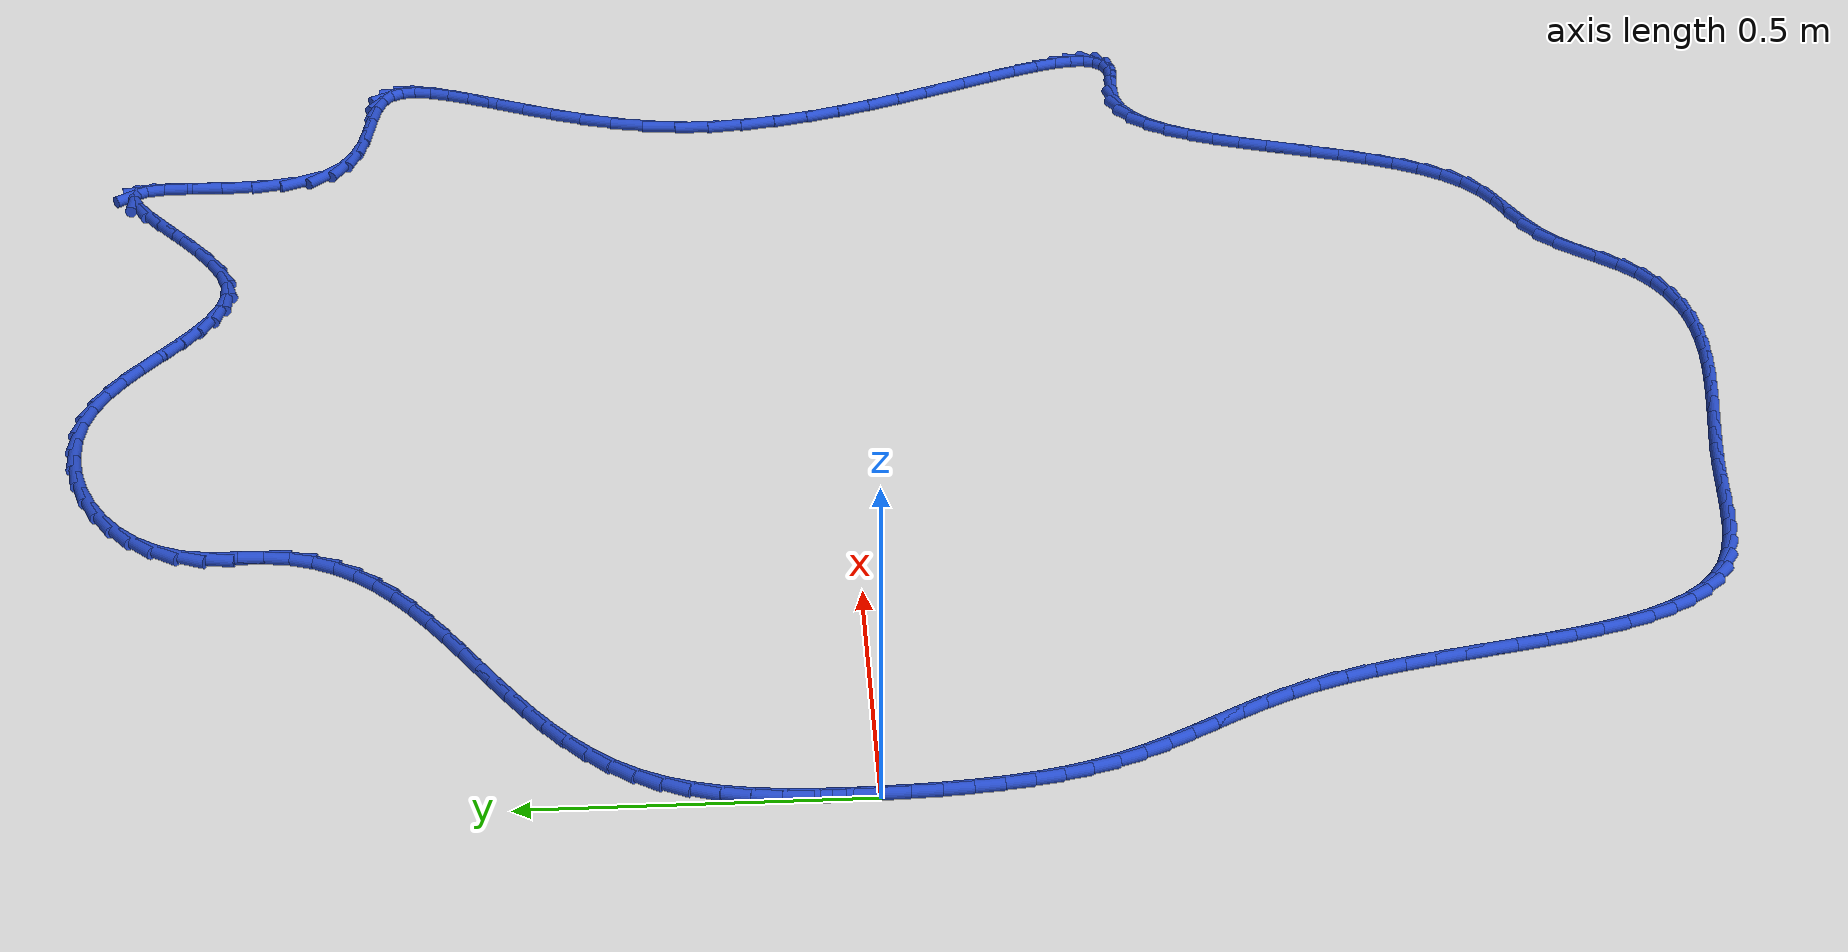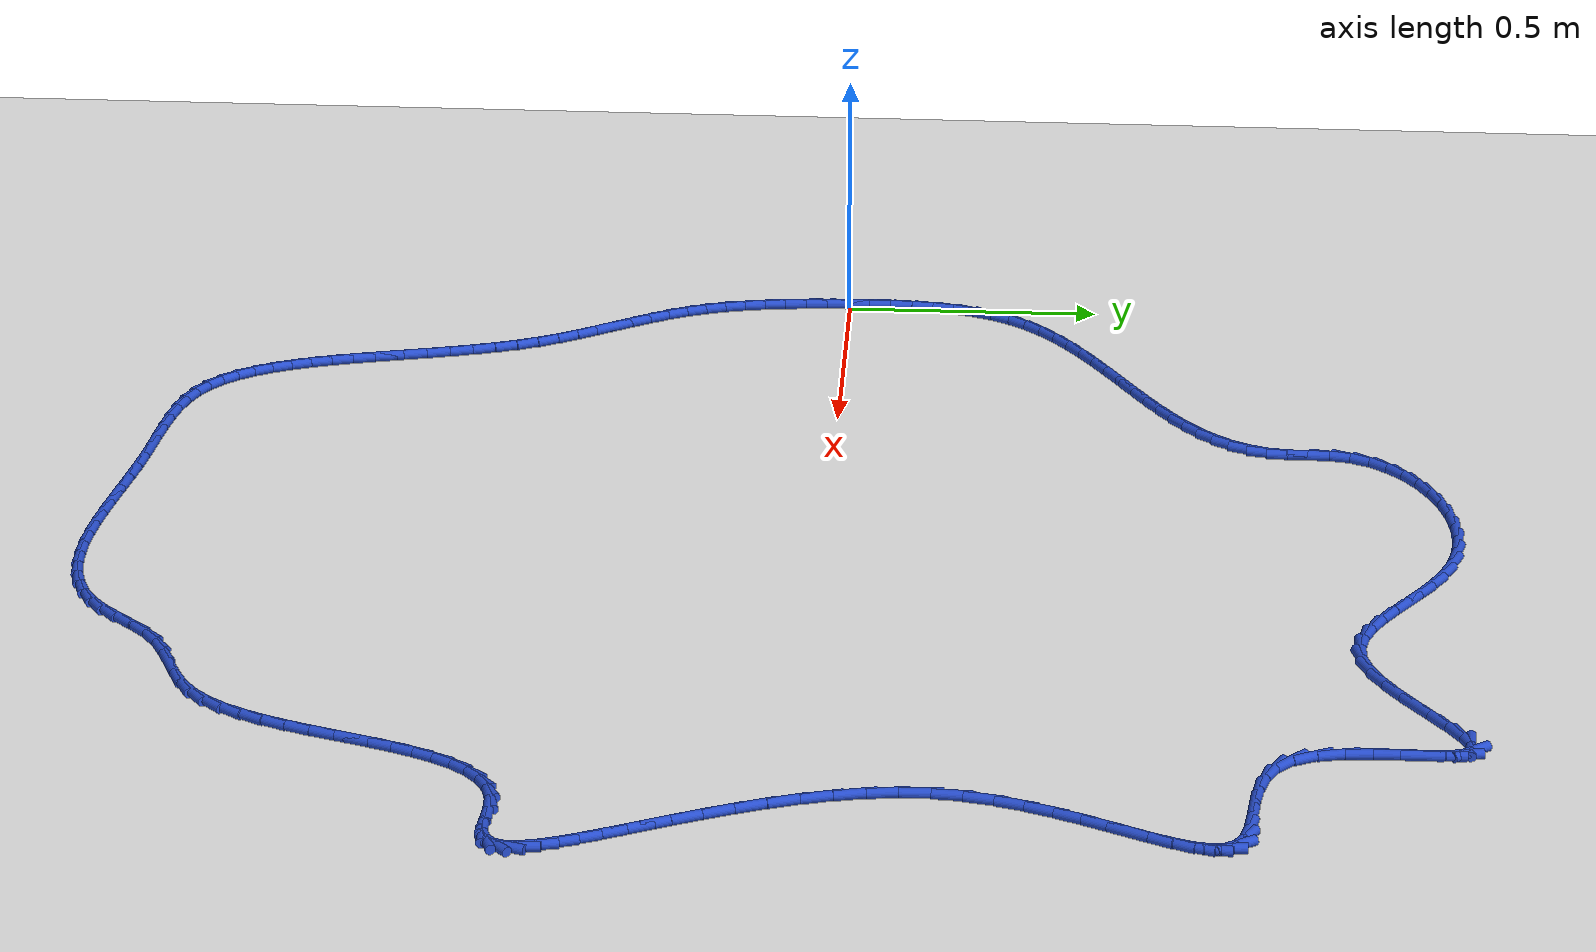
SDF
<sdf version="1.6">
 <world name="default">
  <light name="sun" type="directional">
   <pose>0 0 10 0 -0 0</pose>
   <diffuse>0.8 0.8 0.8 1</diffuse>
   <specular>0.2 0.2 0.2 1</specular>
   <attenuation>
    <range>1000</range>
    <constant>0.9</constant>
    <linear>0.01</linear>
    <quadratic>0.001</quadratic>
   </attenuation>
   <direction>-0.5 0.1 -0.9</direction>
  </light>
  <model name="ground_plane">
   <static>1</static>
   <link name="link">
    <collision name="collision">
     <geometry><plane><normal>0 0 1</normal><size>100 100</size></plane></geometry>
     <surface><friction><ode><mu>100</mu><mu2>50</mu2></ode></friction></surface>
    </collision>
    <visual name="visual">
     <cast_shadows>0</cast_shadows>
     <geometry><plane><normal>0 0 1</normal><size>100 100</size></plane></geometry>
     <material>
      <script><uri>file://media/materials/scripts/gazebo.material</uri><name>Gazebo/WhiteGlow</name></script>
     </material>
    </visual>
   </link>
  </model>
  <gravity>0 0 -9.8</gravity>
  <magnetic_field>6e-06 2.3e-05 -4.2e-05</magnetic_field>
  <atmosphere type="adiabatic"/>
  <physics name="default_physics" default="0" type="ode">
   <max_step_size>0.001</max_step_size>
   <real_time_factor>1</real_time_factor>
   <real_time_update_rate>1000</real_time_update_rate>
  </physics>
  <scene><ambient>0.4 0.4 0.4 1</ambient><background>0.7 0.7 0.7 1</background><shadows>1</shadows></scene>
  <spherical_coordinates>
   <surface_model>EARTH_WGS84</surface_model>
   <latitude_deg>0</latitude_deg>
   <longitude_deg>0</longitude_deg>
   <elevation>0</elevation>
   <heading_deg>0</heading_deg>
  </spherical_coordinates>
  <model name="line">
   <link name="link_0">
    <pose>1.734723475976807e-18 -4.163336342344337e-17 0.01 0 1.57 -1.5516349954841655</pose>
    <collision name="collision">
     <geometry><cylinder><radius>0.01</radius><length>0.08</length></cylinder></geometry>
    </collision>
    <visual name="visual">
     <material>
      <script><name>Gazebo/Blue</name><uri>file://media/materials/scripts/gazebo.material</uri></script>
     </material>
     <geometry><cylinder><radius>0.01</radius><length>0.08</length></cylinder></geometry>
    </visual>
   </link>
   <link name="link_1">
    <pose>-0.0008375539873522851 0.04370528679694738 0.01 0 1.57 1.5622285135951908</pose>
    <collision name="collision">
     <geometry><cylinder><radius>0.01</radius><length>0.08</length></cylinder></geometry>
    </collision>
    <visual name="visual">
     <material>
      <script><name>Gazebo/Blue</name><uri>file://media/materials/scripts/gazebo.material</uri></script>
     </material>
     <geometry><cylinder><radius>0.01</radius><length>0.08</length></cylinder></geometry>
    </visual>
   </link>
   <link name="link_2">
    <pose>-0.00046359046159369344 0.08735170700139451 0.01 0 1.57 1.5220316965582523</pose>
    <collision name="collision">
     <geometry><cylinder><radius>0.01</radius><length>0.08</length></cylinder></geometry>
    </collision>
    <visual name="visual">
     <material>
      <script><name>Gazebo/Blue</name><uri>file://media/materials/scripts/gazebo.material</uri></script>
     </material>
     <geometry><cylinder><radius>0.01</radius><length>0.08</length></cylinder></geometry>
    </visual>
   </link>
   <link name="link_3">
    <pose>0.0016469247286420986 0.13059702614586688 0.01 0 1.57 1.4682887221408003</pose>
    <collision name="collision">
     <geometry><cylinder><radius>0.01</radius><length>0.08</length></cylinder></geometry>
    </collision>
    <visual name="visual">
     <material>
      <script><name>Gazebo/Blue</name><uri>file://media/materials/scripts/gazebo.material</uri></script>
     </material>
     <geometry><cylinder><radius>0.01</radius><length>0.08</length></cylinder></geometry>
    </visual>
   </link>
   <link name="link_4">
    <pose>0.006019025734721422 0.17309900976288986 0.01 0 1.57 1.3996400199315921</pose>
    <collision name="collision">
     <geometry><cylinder><radius>0.01</radius><length>0.08</length></cylinder></geometry>
    </collision>
    <visual name="visual">
     <material>
      <script><name>Gazebo/Blue</name><uri>file://media/materials/scripts/gazebo.material</uri></script>
     </material>
     <geometry><cylinder><radius>0.01</radius><length>0.08</length></cylinder></geometry>
    </visual>
   </link>
   <link name="link_5">
    <pose>0.013177746708010597 0.21451542338498897 0.01 0 1.57 1.3147112211460308</pose>
    <collision name="collision">
     <geometry><cylinder><radius>0.01</radius><length>0.08</length></cylinder></geometry>
    </collision>
    <visual name="visual">
     <material>
      <script><name>Gazebo/Blue</name><uri>file://media/materials/scripts/gazebo.material</uri></script>
     </material>
     <geometry><cylinder><radius>0.01</radius><length>0.08</length></cylinder></geometry>
    </visual>
   </link>
   <link name="link_6">
    <pose>0.023648121799875955 0.2545040325446897 0.01 0 1.57 1.212596981602703</pose>
    <collision name="collision">
     <geometry><cylinder><radius>0.01</radius><length>0.08</length></cylinder></geometry>
    </collision>
    <visual name="visual">
     <material>
      <script><name>Gazebo/Blue</name><uri>file://media/materials/scripts/gazebo.material</uri></script>
     </material>
     <geometry><cylinder><radius>0.01</radius><length>0.08</length></cylinder></geometry>
    </visual>
   </link>
   <link name="link_7">
    <pose>0.03795518516168382 0.29272260277451745 0.01 0 1.57 1.0936099985121328</pose>
    <collision name="collision">
     <geometry><cylinder><radius>0.01</radius><length>0.08</length></cylinder></geometry>
    </collision>
    <visual name="visual">
     <material>
      <script><name>Gazebo/Blue</name><uri>file://media/materials/scripts/gazebo.material</uri></script>
     </material>
     <geometry><cylinder><radius>0.01</radius><length>0.08</length></cylinder></geometry>
    </visual>
   </link>
   <link name="link_8">
    <pose>0.05662366469408644 0.32882906873882023 0.01 0 1.57 0.9673313420640605</pose>
    <collision name="collision">
     <geometry><cylinder><radius>0.01</radius><length>0.08</length></cylinder></geometry>
    </collision>
    <visual name="visual">
     <material>
      <script><name>Gazebo/Blue</name><uri>file://media/materials/scripts/gazebo.material</uri></script>
     </material>
     <geometry><cylinder><radius>0.01</radius><length>0.08</length></cylinder></geometry>
    </visual>
   </link>
   <link name="link_9">
    <pose>0.07991735100679209 0.36262547186658034 0.01 0 1.57 0.8571135771901214</pose>
    <collision name="collision">
     <geometry><cylinder><radius>0.01</radius><length>0.08</length></cylinder></geometry>
    </collision>
    <visual name="visual">
     <material>
      <script><name>Gazebo/Blue</name><uri>file://media/materials/scripts/gazebo.material</uri></script>
     </material>
     <geometry><cylinder><radius>0.01</radius><length>0.08</length></cylinder></geometry>
    </visual>
   </link>
   <link name="link_10">
    <pose>0.107363731733143 0.39432048860368857 0.01 0 1.57 0.7669333815725526</pose>
    <collision name="collision">
     <geometry><cylinder><radius>0.01</radius><length>0.08</length></cylinder></geometry>
    </collision>
    <visual name="visual">
     <material>
      <script><name>Gazebo/Blue</name><uri>file://media/materials/scripts/gazebo.material</uri></script>
     </material>
     <geometry><cylinder><radius>0.01</radius><length>0.08</length></cylinder></geometry>
    </visual>
   </link>
   <link name="link_11">
    <pose>0.1383613501248906 0.4241940069794073 0.01 0 1.57 0.6954750827378042</pose>
    <collision name="collision">
     <geometry><cylinder><radius>0.01</radius><length>0.08</length></cylinder></geometry>
    </collision>
    <visual name="visual">
     <material>
      <script><name>Gazebo/Blue</name><uri>file://media/materials/scripts/gazebo.material</uri></script>
     </material>
     <geometry><cylinder><radius>0.01</radius><length>0.08</length></cylinder></geometry>
    </visual>
   </link>
   <link name="link_12">
    <pose>0.17230874943378613 0.45252591502299905 0.01 0 1.57 0.640822471151388</pose>
    <collision name="collision">
     <geometry><cylinder><radius>0.01</radius><length>0.08</length></cylinder></geometry>
    </collision>
    <visual name="visual">
     <material>
      <script><name>Gazebo/Blue</name><uri>file://media/materials/scripts/gazebo.material</uri></script>
     </material>
     <geometry><cylinder><radius>0.01</radius><length>0.08</length></cylinder></geometry>
    </visual>
   </link>
   <link name="link_13">
    <pose>0.20860447291158105 0.4795961007637258 0.01 0 1.57 0.6011095735560099</pose>
    <collision name="collision">
     <geometry><cylinder><radius>0.01</radius><length>0.08</length></cylinder></geometry>
    </collision>
    <visual name="visual">
     <material>
      <script><name>Gazebo/Blue</name><uri>file://media/materials/scripts/gazebo.material</uri></script>
     </material>
     <geometry><cylinder><radius>0.01</radius><length>0.08</length></cylinder></geometry>
    </visual>
   </link>
   <link name="link_14">
    <pose>0.24664706381002666 0.5056844522308505 0.01 0 1.57 0.574834602583347</pose>
    <collision name="collision">
     <geometry><cylinder><radius>0.01</radius><length>0.08</length></cylinder></geometry>
    </collision>
    <visual name="visual">
     <material>
      <script><name>Gazebo/Blue</name><uri>file://media/materials/scripts/gazebo.material</uri></script>
     </material>
     <geometry><cylinder><radius>0.01</radius><length>0.08</length></cylinder></geometry>
    </visual>
   </link>
   <link name="link_15">
    <pose>0.2858350653808743 0.531070857453635 0.01 0 1.57 0.560982533098376</pose>
    <collision name="collision">
     <geometry><cylinder><radius>0.01</radius><length>0.08</length></cylinder></geometry>
    </collision>
    <visual name="visual">
     <material>
      <script><name>Gazebo/Blue</name><uri>file://media/materials/scripts/gazebo.material</uri></script>
     </material>
     <geometry><cylinder><radius>0.01</radius><length>0.08</length></cylinder></geometry>
    </visual>
   </link>
   <link name="link_16">
    <pose>0.32556702087587536 0.5560352044613422 0.01 0 1.57 0.5590639771397028</pose>
    <collision name="collision">
     <geometry><cylinder><radius>0.01</radius><length>0.08</length></cylinder></geometry>
    </collision>
    <visual name="visual">
     <material>
      <script><name>Gazebo/Blue</name><uri>file://media/materials/scripts/gazebo.material</uri></script>
     </material>
     <geometry><cylinder><radius>0.01</radius><length>0.08</length></cylinder></geometry>
    </visual>
   </link>
   <link name="link_17">
    <pose>0.36524147354678116 0.5808573812832343 0.01 0 1.57 0.5691309588876201</pose>
    <collision name="collision">
     <geometry><cylinder><radius>0.01</radius><length>0.08</length></cylinder></geometry>
    </collision>
    <visual name="visual">
     <material>
      <script><name>Gazebo/Blue</name><uri>file://media/materials/scripts/gazebo.material</uri></script>
     </material>
     <geometry><cylinder><radius>0.01</radius><length>0.08</length></cylinder></geometry>
    </visual>
   </link>
   <link name="link_18">
    <pose>0.4042569666453432 0.6058172759485738 0.01 0 1.57 0.5917969224936898</pose>
    <collision name="collision">
     <geometry><cylinder><radius>0.01</radius><length>0.08</length></cylinder></geometry>
    </collision>
    <visual name="visual">
     <material>
      <script><name>Gazebo/Blue</name><uri>file://media/materials/scripts/gazebo.material</uri></script>
     </material>
     <geometry><cylinder><radius>0.01</radius><length>0.08</length></cylinder></geometry>
    </visual>
   </link>
   <link name="link_19">
    <pose>0.4420120434233125 0.6311947764866226 0.01 0 1.57 0.628264835616634</pose>
    <collision name="collision">
     <geometry><cylinder><radius>0.01</radius><length>0.08</length></cylinder></geometry>
    </collision>
    <visual name="visual">
     <material>
      <script><name>Gazebo/Blue</name><uri>file://media/materials/scripts/gazebo.material</uri></script>
     </material>
     <geometry><cylinder><radius>0.01</radius><length>0.08</length></cylinder></geometry>
    </visual>
   </link>
   <link name="link_20">
    <pose>0.4779052471324406 0.6572697709266437 0.01 0 1.57 0.6803422512708152</pose>
    <collision name="collision">
     <geometry><cylinder><radius>0.01</radius><length>0.08</length></cylinder></geometry>
    </collision>
    <visual name="visual">
     <material>
      <script><name>Gazebo/Blue</name><uri>file://media/materials/scripts/gazebo.material</uri></script>
     </material>
     <geometry><cylinder><radius>0.01</radius><length>0.08</length></cylinder></geometry>
    </visual>
   </link>
   <link name="link_21">
    <pose>0.5113351210244792 0.6843221472978996 0.01 0 1.57 0.7503813735861097</pose>
    <collision name="collision">
     <geometry><cylinder><radius>0.01</radius><length>0.08</length></cylinder></geometry>
    </collision>
    <visual name="visual">
     <material>
      <script><name>Gazebo/Blue</name><uri>file://media/materials/scripts/gazebo.material</uri></script>
     </material>
     <geometry><cylinder><radius>0.01</radius><length>0.08</length></cylinder></geometry>
    </visual>
   </link>
   <link name="link_22">
    <pose>0.541700208351179 0.712631793629652 0.01 0 1.57 0.8410118897159045</pose>
    <collision name="collision">
     <geometry><cylinder><radius>0.01</radius><length>0.08</length></cylinder></geometry>
    </collision>
    <visual name="visual">
     <material>
      <script><name>Gazebo/Blue</name><uri>file://media/materials/scripts/gazebo.material</uri></script>
     </material>
     <geometry><cylinder><radius>0.01</radius><length>0.08</length></cylinder></geometry>
    </visual>
   </link>
   <link name="link_23">
    <pose>0.5683990523642919 0.7424785979511641 0.01 0 1.57 0.9544450644065099</pose>
    <collision name="collision">
     <geometry><cylinder><radius>0.01</radius><length>0.08</length></cylinder></geometry>
    </collision>
    <visual name="visual">
     <material>
      <script><name>Gazebo/Blue</name><uri>file://media/materials/scripts/gazebo.material</uri></script>
     </material>
     <geometry><cylinder><radius>0.01</radius><length>0.08</length></cylinder></geometry>
    </visual>
   </link>
   <link name="link_24">
    <pose>0.5908301963155688 0.7741424482916972 0.01 0 1.57 1.0911283099211424</pose>
    <collision name="collision">
     <geometry><cylinder><radius>0.01</radius><length>0.08</length></cylinder></geometry>
    </collision>
    <visual name="visual">
     <material>
      <script><name>Gazebo/Blue</name><uri>file://media/materials/scripts/gazebo.material</uri></script>
     </material>
     <geometry><cylinder><radius>0.01</radius><length>0.08</length></cylinder></geometry>
    </visual>
   </link>
   <link name="link_25">
    <pose>0.6083921834567613 0.8079032326805149 0.01 0 1.57 1.2479129136948601</pose>
    <collision name="collision">
     <geometry><cylinder><radius>0.01</radius><length>0.08</length></cylinder></geometry>
    </collision>
    <visual name="visual">
     <material>
      <script><name>Gazebo/Blue</name><uri>file://media/materials/scripts/gazebo.material</uri></script>
     </material>
     <geometry><cylinder><radius>0.01</radius><length>0.08</length></cylinder></geometry>
    </visual>
   </link>
   <link name="link_26">
    <pose>0.6204835570396209 0.8440408391468792 0.01 0 1.57 1.4168643602684037</pose>
    <collision name="collision">
     <geometry><cylinder><radius>0.01</radius><length>0.08</length></cylinder></geometry>
    </collision>
    <visual name="visual">
     <material>
      <script><name>Gazebo/Blue</name><uri>file://media/materials/scripts/gazebo.material</uri></script>
     </material>
     <geometry><cylinder><radius>0.01</radius><length>0.08</length></cylinder></geometry>
    </visual>
   </link>
   <link name="link_27">
    <pose>0.6265028603158986 0.8828351557200522 0.01 0 1.57 1.562119282736221</pose>
    <collision name="collision">
     <geometry><cylinder><radius>0.01</radius><length>0.08</length></cylinder></geometry>
    </collision>
    <visual name="visual">
     <material>
      <script><name>Gazebo/Blue</name><uri>file://media/materials/scripts/gazebo.material</uri></script>
     </material>
     <geometry><cylinder><radius>0.01</radius><length>0.08</length></cylinder></geometry>
    </visual>
   </link>
   <link name="link_28">
    <pose>0.6268619812969292 0.9242215962735912 0.01 0 1.57 1.5625889475262384</pose>
    <collision name="collision">
     <geometry><cylinder><radius>0.01</radius><length>0.08</length></cylinder></geometry>
    </collision>
    <visual name="visual">
     <material>
      <script><name>Gazebo/Blue</name><uri>file://media/materials/scripts/gazebo.material</uri></script>
     </material>
     <geometry><cylinder><radius>0.01</radius><length>0.08</length></cylinder></geometry>
    </visual>
   </link>
   <link name="link_29">
    <pose>0.6272078021137899 0.9663560024649213 0.01 0 1.57 1.3935737563570456</pose>
    <collision name="collision">
     <geometry><cylinder><radius>0.01</radius><length>0.08</length></cylinder></geometry>
    </collision>
    <visual name="visual">
     <material>
      <script><name>Gazebo/Blue</name><uri>file://media/materials/scripts/gazebo.material</uri></script>
     </material>
     <geometry><cylinder><radius>0.01</radius><length>0.08</length></cylinder></geometry>
    </visual>
   </link>
   <link name="link_30">
    <pose>0.6344724781294213 1.0069177680674832 0.01 0 1.57 1.1639107024751971</pose>
    <collision name="collision">
     <geometry><cylinder><radius>0.01</radius><length>0.08</length></cylinder></geometry>
    </collision>
    <visual name="visual">
     <material>
      <script><name>Gazebo/Blue</name><uri>file://media/materials/scripts/gazebo.material</uri></script>
     </material>
     <geometry><cylinder><radius>0.01</radius><length>0.08</length></cylinder></geometry>
    </visual>
   </link>
   <link name="link_31">
    <pose>0.6507744069647059 1.0447471053343562 0.01 0 1.57 0.9604710027419516</pose>
    <collision name="collision">
     <geometry><cylinder><radius>0.01</radius><length>0.08</length></cylinder></geometry>
    </collision>
    <visual name="visual">
     <material>
      <script><name>Gazebo/Blue</name><uri>file://media/materials/scripts/gazebo.material</uri></script>
     </material>
     <geometry><cylinder><radius>0.01</radius><length>0.08</length></cylinder></geometry>
    </visual>
   </link>
   <link name="link_32">
    <pose>0.6750472994294157 1.0794522539602032 0.01 0 1.57 0.7867143735615041</pose>
    <collision name="collision">
     <geometry><cylinder><radius>0.01</radius><length>0.08</length></cylinder></geometry>
    </collision>
    <visual name="visual">
     <material>
      <script><name>Gazebo/Blue</name><uri>file://media/materials/scripts/gazebo.material</uri></script>
     </material>
     <geometry><cylinder><radius>0.01</radius><length>0.08</length></cylinder></geometry>
    </visual>
   </link>
   <link name="link_33">
    <pose>0.7061681466164945 1.1106551323156735 0.01 0 1.57 0.6380628842356526</pose>
    <collision name="collision">
     <geometry><cylinder><radius>0.01</radius><length>0.08</length></cylinder></geometry>
    </collision>
    <visual name="visual">
     <material>
      <script><name>Gazebo/Blue</name><uri>file://media/materials/scripts/gazebo.material</uri></script>
     </material>
     <geometry><cylinder><radius>0.01</radius><length>0.08</length></cylinder></geometry>
    </visual>
   </link>
   <link name="link_34">
    <pose>0.7430139396188868 1.137977658771415 0.01 0 1.57 0.5077910132675795</pose>
    <collision name="collision">
     <geometry><cylinder><radius>0.01</radius><length>0.08</length></cylinder></geometry>
    </collision>
    <visual name="visual">
     <material>
      <script><name>Gazebo/Blue</name><uri>file://media/materials/scripts/gazebo.material</uri></script>
     </material>
     <geometry><cylinder><radius>0.01</radius><length>0.08</length></cylinder></geometry>
    </visual>
   </link>
   <link name="link_35">
    <pose>0.7844616695295357 1.1610417516980769 0.01 0 1.57 0.3892429577701108</pose>
    <collision name="collision">
     <geometry><cylinder><radius>0.01</radius><length>0.08</length></cylinder></geometry>
    </collision>
    <visual name="visual">
     <material>
      <script><name>Gazebo/Blue</name><uri>file://media/materials/scripts/gazebo.material</uri></script>
     </material>
     <geometry><cylinder><radius>0.01</radius><length>0.08</length></cylinder></geometry>
    </visual>
   </link>
   <link name="link_36">
    <pose>0.8293883274413849 1.179469329466307 0.01 0 1.57 0.27641514583940036</pose>
    <collision name="collision">
     <geometry><cylinder><radius>0.01</radius><length>0.08</length></cylinder></geometry>
    </collision>
    <visual name="visual">
     <material>
      <script><name>Gazebo/Blue</name><uri>file://media/materials/scripts/gazebo.material</uri></script>
     </material>
     <geometry><cylinder><radius>0.01</radius><length>0.08</length></cylinder></geometry>
    </visual>
   </link>
   <link name="link_37">
    <pose>0.8766709044473785 1.1928823104467547 0.01 0 1.57 0.16383254843054224</pose>
    <collision name="collision">
     <geometry><cylinder><radius>0.01</radius><length>0.08</length></cylinder></geometry>
    </collision>
    <visual name="visual">
     <material>
      <script><name>Gazebo/Blue</name><uri>file://media/materials/scripts/gazebo.material</uri></script>
     </material>
     <geometry><cylinder><radius>0.01</radius><length>0.08</length></cylinder></geometry>
    </visual>
   </link>
   <link name="link_38">
    <pose>0.9251863916404601 1.2009026130100682 0.01 0 1.57 0.046229753475823136</pose>
    <collision name="collision">
     <geometry><cylinder><radius>0.01</radius><length>0.08</length></cylinder></geometry>
    </collision>
    <visual name="visual">
     <material>
      <script><name>Gazebo/Blue</name><uri>file://media/materials/scripts/gazebo.material</uri></script>
     </material>
     <geometry><cylinder><radius>0.01</radius><length>0.08</length></cylinder></geometry>
    </visual>
   </link>
   <link name="link_39">
    <pose>0.9738117801135738 1.2031521555268958 0.01 0 1.57 -0.08171455629872709</pose>
    <collision name="collision">
     <geometry><cylinder><radius>0.01</radius><length>0.08</length></cylinder></geometry>
    </collision>
    <visual name="visual">
     <material>
      <script><name>Gazebo/Blue</name><uri>file://media/materials/scripts/gazebo.material</uri></script>
     </material>
     <geometry><cylinder><radius>0.01</radius><length>0.08</length></cylinder></geometry>
    </visual>
   </link>
   <link name="link_40">
    <pose>1.0214240609596634 1.199252856367887 0.01 0 1.57 -0.22528909483939474</pose>
    <collision name="collision">
     <geometry><cylinder><radius>0.01</radius><length>0.08</length></cylinder></geometry>
    </collision>
    <visual name="visual">
     <material>
      <script><name>Gazebo/Blue</name><uri>file://media/materials/scripts/gazebo.material</uri></script>
     </material>
     <geometry><cylinder><radius>0.01</radius><length>0.08</length></cylinder></geometry>
    </visual>
   </link>
   <link name="link_41">
    <pose>1.0669028967350735 1.1888300336523996 0.01 0 1.57 -0.3730333630170915</pose>
    <collision name="collision">
     <geometry><cylinder><radius>0.01</radius><length>0.08</length></cylinder></geometry>
    </collision>
    <visual name="visual">
     <material>
      <script><name>Gazebo/Blue</name><uri>file://media/materials/scripts/gazebo.material</uri></script>
     </material>
     <geometry><cylinder><radius>0.01</radius><length>0.08</length></cylinder></geometry>
    </visual>
   </link>
   <link name="link_42">
    <pose>1.1096062982664967 1.1721177594563281 0.01 0 1.57 -0.4891935609033027</pose>
    <collision name="collision">
     <geometry><cylinder><radius>0.01</radius><length>0.08</length></cylinder></geometry>
    </collision>
    <visual name="visual">
     <material>
      <script><name>Gazebo/Blue</name><uri>file://media/materials/scripts/gazebo.material</uri></script>
     </material>
     <geometry><cylinder><radius>0.01</radius><length>0.08</length></cylinder></geometry>
    </visual>
   </link>
   <link name="link_43">
    <pose>1.1499192502585034 1.150657049875582 0.01 0 1.57 -0.5674120787454867</pose>
    <collision name="collision">
     <geometry><cylinder><radius>0.01</radius><length>0.08</length></cylinder></geometry>
    </collision>
    <visual name="visual">
     <material>
      <script><name>Gazebo/Blue</name><uri>file://media/materials/scripts/gazebo.material</uri></script>
     </material>
     <geometry><cylinder><radius>0.01</radius><length>0.08</length></cylinder></geometry>
    </visual>
   </link>
   <link name="link_44">
    <pose>1.188359657382814 1.1261580771647128 0.01 0 1.57 -0.6083154921437188</pose>
    <collision name="collision">
     <geometry><cylinder><radius>0.01</radius><length>0.08</length></cylinder></geometry>
    </collision>
    <visual name="visual">
     <material>
      <script><name>Gazebo/Blue</name><uri>file://media/materials/scripts/gazebo.material</uri></script>
     </material>
     <geometry><cylinder><radius>0.01</radius><length>0.08</length></cylinder></geometry>
    </visual>
   </link>
   <link name="link_45">
    <pose>1.2254454243111492 1.1003310135782736 0.01 0 1.57 -0.6120330214751345</pose>
    <collision name="collision">
     <geometry><cylinder><radius>0.01</radius><length>0.08</length></cylinder></geometry>
    </collision>
    <visual name="visual">
     <material>
      <script><name>Gazebo/Blue</name><uri>file://media/materials/scripts/gazebo.material</uri></script>
     </material>
     <geometry><cylinder><radius>0.01</radius><length>0.08</length></cylinder></geometry>
    </visual>
   </link>
   <link name="link_46">
    <pose>1.26169445571523 1.0748860313708168 0.01 0 1.57 -0.5763380105706445</pose>
    <collision name="collision">
     <geometry><cylinder><radius>0.01</radius><length>0.08</length></cylinder></geometry>
    </collision>
    <visual name="visual">
     <material>
      <script><name>Gazebo/Blue</name><uri>file://media/materials/scripts/gazebo.material</uri></script>
     </material>
     <geometry><cylinder><radius>0.01</radius><length>0.08</length></cylinder></geometry>
    </visual>
   </link>
   <link name="link_47">
    <pose>1.2976246562667768 1.0515333027968943 0.01 0 1.57 -0.49600063560847657</pose>
    <collision name="collision">
     <geometry><cylinder><radius>0.01</radius><length>0.08</length></cylinder></geometry>
    </collision>
    <visual name="visual">
     <material>
      <script><name>Gazebo/Blue</name><uri>file://media/materials/scripts/gazebo.material</uri></script>
     </material>
     <geometry><cylinder><radius>0.01</radius><length>0.08</length></cylinder></geometry>
    </visual>
   </link>
   <link name="link_48">
    <pose>1.3337539306375097 1.0319830001110581 0.01 0 1.57 -0.36400352843014955</pose>
    <collision name="collision">
     <geometry><cylinder><radius>0.01</radius><length>0.08</length></cylinder></geometry>
    </collision>
    <visual name="visual">
     <material>
      <script><name>Gazebo/Blue</name><uri>file://media/materials/scripts/gazebo.material</uri></script>
     </material>
     <geometry><cylinder><radius>0.01</radius><length>0.08</length></cylinder></geometry>
    </visual>
   </link>
   <link name="link_49">
    <pose>1.3706001834991504 1.0179452955678614 0.01 0 1.57 -0.17708371613022572</pose>
    <collision name="collision">
     <geometry><cylinder><radius>0.01</radius><length>0.08</length></cylinder></geometry>
    </collision>
    <visual name="visual">
     <material>
      <script><name>Gazebo/Blue</name><uri>file://media/materials/scripts/gazebo.material</uri></script>
     </material>
     <geometry><cylinder><radius>0.01</radius><length>0.08</length></cylinder></geometry>
    </visual>
   </link>
   <link name="link_50">
    <pose>1.4086813195234185 1.0111303614218556 0.01 0 1.57 0.053120950739556694</pose>
    <collision name="collision">
     <geometry><cylinder><radius>0.01</radius><length>0.08</length></cylinder></geometry>
    </collision>
    <visual name="visual">
     <material>
      <script><name>Gazebo/Blue</name><uri>file://media/materials/scripts/gazebo.material</uri></script>
     </material>
     <geometry><cylinder><radius>0.01</radius><length>0.08</length></cylinder></geometry>
    </visual>
   </link>
   <link name="link_51">
    <pose>1.4485152433820359 1.0132483699275934 0.01 0 1.57 0.2912948138718969</pose>
    <collision name="collision">
     <geometry><cylinder><radius>0.01</radius><length>0.08</length></cylinder></geometry>
    </collision>
    <visual name="visual">
     <material>
      <script><name>Gazebo/Blue</name><uri>file://media/materials/scripts/gazebo.material</uri></script>
     </material>
     <geometry><cylinder><radius>0.01</radius><length>0.08</length></cylinder></geometry>
    </visual>
   </link>
   <link name="link_52">
    <pose>1.4905637073971858 1.025855485463928 0.01 0 1.57 0.46709459196604697</pose>
    <collision name="collision">
     <geometry><cylinder><radius>0.01</radius><length>0.08</length></cylinder></geometry>
    </collision>
    <visual name="visual">
     <material>
      <script><name>Gazebo/Blue</name><uri>file://media/materials/scripts/gazebo.material</uri></script>
     </material>
     <geometry><cylinder><radius>0.01</radius><length>0.08</length></cylinder></geometry>
    </visual>
   </link>
   <link name="link_53">
    <pose>1.534351632615425 1.047938444846299 0.01 0 1.57 0.5706663986711314</pose>
    <collision name="collision">
     <geometry><cylinder><radius>0.01</radius><length>0.08</length></cylinder></geometry>
    </collision>
    <visual name="visual">
     <material>
      <script><name>Gazebo/Blue</name><uri>file://media/materials/scripts/gazebo.material</uri></script>
     </material>
     <geometry><cylinder><radius>0.01</radius><length>0.08</length></cylinder></geometry>
    </visual>
   </link>
   <link name="link_54">
    <pose>1.5786299132699726 1.0763610777234653 0.01 0 1.57 0.6277244070314754</pose>
    <collision name="collision">
     <geometry><cylinder><radius>0.01</radius><length>0.08</length></cylinder></geometry>
    </collision>
    <visual name="visual">
     <material>
      <script><name>Gazebo/Blue</name><uri>file://media/materials/scripts/gazebo.material</uri></script>
     </material>
     <geometry><cylinder><radius>0.01</radius><length>0.08</length></cylinder></geometry>
    </visual>
   </link>
   <link name="link_55">
    <pose>1.6221262245512973 1.10792353136082 0.01 0 1.57 0.6499696890139711</pose>
    <collision name="collision">
     <geometry><cylinder><radius>0.01</radius><length>0.08</length></cylinder></geometry>
    </collision>
    <visual name="visual">
     <material>
      <script><name>Gazebo/Blue</name><uri>file://media/materials/scripts/gazebo.material</uri></script>
     </material>
     <geometry><cylinder><radius>0.01</radius><length>0.08</length></cylinder></geometry>
    </visual>
   </link>
   <link name="link_56">
    <pose>1.6635682416498665 1.1394259530237572 0.01 0 1.57 0.6376997019563035</pose>
    <collision name="collision">
     <geometry><cylinder><radius>0.01</radius><length>0.08</length></cylinder></geometry>
    </collision>
    <visual name="visual">
     <material>
      <script><name>Gazebo/Blue</name><uri>file://media/materials/scripts/gazebo.material</uri></script>
     </material>
     <geometry><cylinder><radius>0.01</radius><length>0.08</length></cylinder></geometry>
    </visual>
   </link>
   <link name="link_57">
    <pose>1.70168363975615 1.1676684899776708 0.01 0 1.57 0.5763144807700443</pose>
    <collision name="collision">
     <geometry><cylinder><radius>0.01</radius><length>0.08</length></cylinder></geometry>
    </collision>
    <visual name="visual">
     <material>
      <script><name>Gazebo/Blue</name><uri>file://media/materials/scripts/gazebo.material</uri></script>
     </material>
     <geometry><cylinder><radius>0.01</radius><length>0.08</length></cylinder></geometry>
    </visual>
   </link>
   <link name="link_58">
    <pose>1.7352000940606152 1.189451289487955 0.01 0 1.57 0.4132736091215912</pose>
    <collision name="collision">
     <geometry><cylinder><radius>0.01</radius><length>0.08</length></cylinder></geometry>
    </collision>
    <visual name="visual">
     <material>
      <script><name>Gazebo/Blue</name><uri>file://media/materials/scripts/gazebo.material</uri></script>
     </material>
     <geometry><cylinder><radius>0.01</radius><length>0.08</length></cylinder></geometry>
    </visual>
   </link>
   <link name="link_59">
    <pose>1.7628452797537293 1.2015744988200023 0.01 0 1.57 -0.03589561886949671</pose>
    <collision name="collision">
     <geometry><cylinder><radius>0.01</radius><length>0.08</length></cylinder></geometry>
    </collision>
    <visual name="visual">
     <material>
      <script><name>Gazebo/Blue</name><uri>file://media/materials/scripts/gazebo.material</uri></script>
     </material>
     <geometry><cylinder><radius>0.01</radius><length>0.08</length></cylinder></geometry>
    </visual>
   </link>
   <link name="link_60">
    <pose>1.7833468720259624 1.2008382652392073 0.01 0 1.57 -0.9226782099739248</pose>
    <collision name="collision">
     <geometry><cylinder><radius>0.01</radius><length>0.08</length></cylinder></geometry>
    </collision>
    <visual name="visual">
     <material>
      <script><name>Gazebo/Blue</name><uri>file://media/materials/scripts/gazebo.material</uri></script>
     </material>
     <geometry><cylinder><radius>0.01</radius><length>0.08</length></cylinder></geometry>
    </visual>
   </link>
   <link name="link_61">
    <pose>1.795703123769249 1.1845207636618194 0.01 0 1.57 -1.3897188025791753</pose>
    <collision name="collision">
     <geometry><cylinder><radius>0.01</radius><length>0.08</length></cylinder></geometry>
    </collision>
    <visual name="visual">
     <material>
      <script><name>Gazebo/Blue</name><uri>file://media/materials/scripts/gazebo.material</uri></script>
     </material>
     <geometry><cylinder><radius>0.01</radius><length>0.08</length></cylinder></geometry>
    </visual>
   </link>
   <link name="link_62">
    <pose>1.801276769686214 1.1540774817661033 0.01 0 1.57 -1.5372298876736168</pose>
    <collision name="collision">
     <geometry><cylinder><radius>0.01</radius><length>0.08</length></cylinder></geometry>
    </collision>
    <visual name="visual">
     <material>
      <script><name>Gazebo/Blue</name><uri>file://media/materials/scripts/gazebo.material</uri></script>
     </material>
     <geometry><cylinder><radius>0.01</radius><length>0.08</length></cylinder></geometry>
    </visual>
   </link>
   <link name="link_63">
    <pose>1.80265201997051 1.1131218790675736 0.01 0 1.57 1.566015073553247</pose>
    <collision name="collision">
     <geometry><cylinder><radius>0.01</radius><length>0.08</length></cylinder></geometry>
    </collision>
    <visual name="visual">
     <material>
      <script><name>Gazebo/Blue</name><uri>file://media/materials/scripts/gazebo.material</uri></script>
     </material>
     <geometry><cylinder><radius>0.01</radius><length>0.08</length></cylinder></geometry>
    </visual>
   </link>
   <link name="link_64">
    <pose>1.8024233002060286 1.0652854625371406 0.01 0 1.57 -1.5558864992763892</pose>
    <collision name="collision">
     <geometry><cylinder><radius>0.01</radius><length>0.08</length></cylinder></geometry>
    </collision>
    <visual name="visual">
     <material>
      <script><name>Gazebo/Blue</name><uri>file://media/materials/scripts/gazebo.material</uri></script>
     </material>
     <geometry><cylinder><radius>0.01</radius><length>0.08</length></cylinder></geometry>
    </visual>
   </link>
   <link name="link_65">
    <pose>1.8031850359766608 1.014199739145715 0.01 0 1.57 -1.485279274026279</pose>
    <collision name="collision">
     <geometry><cylinder><radius>0.01</radius><length>0.08</length></cylinder></geometry>
    </collision>
    <visual name="visual">
     <material>
      <script><name>Gazebo/Blue</name><uri>file://media/materials/scripts/gazebo.material</uri></script>
     </material>
     <geometry><cylinder><radius>0.01</radius><length>0.08</length></cylinder></geometry>
    </visual>
   </link>
   <link name="link_66">
    <pose>1.8075316528662984 0.9634962158642075 0.01 0 1.57 -1.349059631537695</pose>
    <collision name="collision">
     <geometry><cylinder><radius>0.01</radius><length>0.08</length></cylinder></geometry>
    </collision>
    <visual name="visual">
     <material>
      <script><name>Gazebo/Blue</name><uri>file://media/materials/scripts/gazebo.material</uri></script>
     </material>
     <geometry><cylinder><radius>0.01</radius><length>0.08</length></cylinder></geometry>
    </visual>
   </link>
   <link name="link_67">
    <pose>1.8180575764588318 0.9168063996635276 0.01 0 1.57 -1.1117209787946738</pose>
    <collision name="collision">
     <geometry><cylinder><radius>0.01</radius><length>0.08</length></cylinder></geometry>
    </collision>
    <visual name="visual">
     <material>
      <script><name>Gazebo/Blue</name><uri>file://media/materials/scripts/gazebo.material</uri></script>
     </material>
     <geometry><cylinder><radius>0.01</radius><length>0.08</length></cylinder></geometry>
    </visual>
   </link>
   <link name="link_68">
    <pose>1.8373572323381522 0.8777617975145865 0.01 0 1.57 -0.7566590972441934</pose>
    <collision name="collision">
     <geometry><cylinder><radius>0.01</radius><length>0.08</length></cylinder></geometry>
    </collision>
    <visual name="visual">
     <material>
      <script><name>Gazebo/Blue</name><uri>file://media/materials/scripts/gazebo.material</uri></script>
     </material>
     <geometry><cylinder><radius>0.01</radius><length>0.08</length></cylinder></geometry>
    </visual>
   </link>
   <link name="link_69">
    <pose>1.8674269218202773 0.8493726238579378 0.01 0 1.57 -0.4471492917470675</pose>
    <collision name="collision">
     <geometry><cylinder><radius>0.01</radius><length>0.08</length></cylinder></geometry>
    </collision>
    <visual name="visual">
     <material>
      <script><name>Gazebo/Blue</name><uri>file://media/materials/scripts/gazebo.material</uri></script>
     </material>
     <geometry><cylinder><radius>0.01</radius><length>0.08</length></cylinder></geometry>
    </visual>
   </link>
   <link name="link_70">
    <pose>1.9064308257885931 0.8306685360357183 0.01 0 1.57 -0.25365262705605074</pose>
    <collision name="collision">
     <geometry><cylinder><radius>0.01</radius><length>0.08</length></cylinder></geometry>
    </collision>
    <visual name="visual">
     <material>
      <script><name>Gazebo/Blue</name><uri>file://media/materials/scripts/gazebo.material</uri></script>
     </material>
     <geometry><cylinder><radius>0.01</radius><length>0.08</length></cylinder></geometry>
    </visual>
   </link>
   <link name="link_71">
    <pose>1.9510214991236716 0.8191090127588253 0.01 0 1.57 -0.14753956772271795</pose>
    <collision name="collision">
     <geometry><cylinder><radius>0.01</radius><length>0.08</length></cylinder></geometry>
    </collision>
    <visual name="visual">
     <material>
      <script><name>Gazebo/Blue</name><uri>file://media/materials/scripts/gazebo.material</uri></script>
     </material>
     <geometry><cylinder><radius>0.01</radius><length>0.08</length></cylinder></geometry>
    </visual>
   </link>
   <link name="link_72">
    <pose>1.9978478149712071 0.8121497083917767 0.01 0 1.57 -0.10686202392522685</pose>
    <collision name="collision">
     <geometry><cylinder><radius>0.01</radius><length>0.08</length></cylinder></geometry>
    </collision>
    <visual name="visual">
     <material>
      <script><name>Gazebo/Blue</name><uri>file://media/materials/scripts/gazebo.material</uri></script>
     </material>
     <geometry><cylinder><radius>0.01</radius><length>0.08</length></cylinder></geometry>
    </visual>
   </link>
   <link name="link_73">
    <pose>2.043558646476893 0.8072462772990899 0.01 0 1.57 -0.1299939142345705</pose>
    <collision name="collision">
     <geometry><cylinder><radius>0.01</radius><length>0.08</length></cylinder></geometry>
    </collision>
    <visual name="visual">
     <material>
      <script><name>Gazebo/Blue</name><uri>file://media/materials/scripts/gazebo.material</uri></script>
     </material>
     <geometry><cylinder><radius>0.01</radius><length>0.08</length></cylinder></geometry>
    </visual>
   </link>
   <link name="link_74">
    <pose>2.0848028667864247 0.8018543738452828 0.01 0 1.57 -0.2468952321997783</pose>
    <collision name="collision">
     <geometry><cylinder><radius>0.01</radius><length>0.08</length></cylinder></geometry>
    </collision>
    <visual name="visual">
     <material>
      <script><name>Gazebo/Blue</name><uri>file://media/materials/scripts/gazebo.material</uri></script>
     </material>
     <geometry><cylinder><radius>0.01</radius><length>0.08</length></cylinder></geometry>
    </visual>
   </link>
   <link name="link_75">
    <pose>2.1182293490454946 0.7934296523948727 0.01 0 1.57 -0.5438593795783099</pose>
    <collision name="collision">
     <geometry><cylinder><radius>0.01</radius><length>0.08</length></cylinder></geometry>
    </collision>
    <visual name="visual">
     <material>
      <script><name>Gazebo/Blue</name><uri>file://media/materials/scripts/gazebo.material</uri></script>
     </material>
     <geometry><cylinder><radius>0.01</radius><length>0.08</length></cylinder></geometry>
    </visual>
   </link>
   <link name="link_76">
    <pose>2.1409323989203535 0.7797013921637017 0.01 0 1.57 -1.0131340074453357</pose>
    <collision name="collision">
     <geometry><cylinder><radius>0.01</radius><length>0.08</length></cylinder></geometry>
    </collision>
    <visual name="visual">
     <material>
      <script><name>Gazebo/Blue</name><uri>file://media/materials/scripts/gazebo.material</uri></script>
     </material>
     <geometry><cylinder><radius>0.01</radius><length>0.08</length></cylinder></geometry>
    </visual>
   </link>
   <link name="link_77">
    <pose>2.1530518826237985 0.7602697304960382 0.01 0 1.57 -1.4521743615835185</pose>
    <collision name="collision">
     <geometry><cylinder><radius>0.01</radius><length>0.08</length></cylinder></geometry>
    </collision>
    <visual name="visual">
     <material>
      <script><name>Gazebo/Blue</name><uri>file://media/materials/scripts/gazebo.material</uri></script>
     </material>
     <geometry><cylinder><radius>0.01</radius><length>0.08</length></cylinder></geometry>
    </visual>
   </link>
   <link name="link_78">
    <pose>2.156001885180525 0.7355175449198376 0.01 0 1.57 1.4104618495751808</pose>
    <collision name="collision">
     <geometry><cylinder><radius>0.01</radius><length>0.08</length></cylinder></geometry>
    </collision>
    <visual name="visual">
     <material>
      <script><name>Gazebo/Blue</name><uri>file://media/materials/scripts/gazebo.material</uri></script>
     </material>
     <geometry><cylinder><radius>0.01</radius><length>0.08</length></cylinder></geometry>
    </visual>
   </link>
   <link name="link_79">
    <pose>2.15120079375677 0.7058303557266292 0.01 0 1.57 1.2563826910621199</pose>
    <collision name="collision">
     <geometry><cylinder><radius>0.01</radius><length>0.08</length></cylinder></geometry>
    </collision>
    <visual name="visual">
     <material>
      <script><name>Gazebo/Blue</name><uri>file://media/materials/scripts/gazebo.material</uri></script>
     </material>
     <geometry><cylinder><radius>0.01</radius><length>0.08</length></cylinder></geometry>
    </visual>
   </link>
   <link name="link_80">
    <pose>2.1400669955187714 0.6715936832079424 0.01 0 1.57 1.1749438660977565</pose>
    <collision name="collision">
     <geometry><cylinder><radius>0.01</radius><length>0.08</length></cylinder></geometry>
    </collision>
    <visual name="visual">
     <material>
      <script><name>Gazebo/Blue</name><uri>file://media/materials/scripts/gazebo.material</uri></script>
     </material>
     <geometry><cylinder><radius>0.01</radius><length>0.08</length></cylinder></geometry>
    </visual>
   </link>
   <link name="link_81">
    <pose>2.124018877632766 0.6331930476553054 0.01 0 1.57 1.1368888580453014</pose>
    <collision name="collision">
     <geometry><cylinder><radius>0.01</radius><length>0.08</length></cylinder></geometry>
    </collision>
    <visual name="visual">
     <material>
      <script><name>Gazebo/Blue</name><uri>file://media/materials/scripts/gazebo.material</uri></script>
     </material>
     <geometry><cylinder><radius>0.01</radius><length>0.08</length></cylinder></geometry>
    </visual>
   </link>
   <link name="link_82">
    <pose>2.1044748272649905 0.5910139693602473 0.01 0 1.57 1.1277975543776535</pose>
    <collision name="collision">
     <geometry><cylinder><radius>0.01</radius><length>0.08</length></cylinder></geometry>
    </collision>
    <visual name="visual">
     <material>
      <script><name>Gazebo/Blue</name><uri>file://media/materials/scripts/gazebo.material</uri></script>
     </material>
     <geometry><cylinder><radius>0.01</radius><length>0.08</length></cylinder></geometry>
    </visual>
   </link>
   <link name="link_83">
    <pose>2.0828532315816832 0.5454419686142977 0.01 0 1.57 1.14077560575886</pose>
    <collision name="collision">
     <geometry><cylinder><radius>0.01</radius><length>0.08</length></cylinder></geometry>
    </collision>
    <visual name="visual">
     <material>
      <script><name>Gazebo/Blue</name><uri>file://media/materials/scripts/gazebo.material</uri></script>
     </material>
     <geometry><cylinder><radius>0.01</radius><length>0.08</length></cylinder></geometry>
    </visual>
   </link>
   <link name="link_84">
    <pose>2.06057247774908 0.4968625657089848 0.01 0 1.57 1.1728863777894047</pose>
    <collision name="collision">
     <geometry><cylinder><radius>0.01</radius><length>0.08</length></cylinder></geometry>
    </collision>
    <visual name="visual">
     <material>
      <script><name>Gazebo/Blue</name><uri>file://media/materials/scripts/gazebo.material</uri></script>
     </material>
     <geometry><cylinder><radius>0.01</radius><length>0.08</length></cylinder></geometry>
    </visual>
   </link>
   <link name="link_85">
    <pose>2.039050952933419 0.4456612809358376 0.01 0 1.57 1.2234799303606845</pose>
    <collision name="collision">
     <geometry><cylinder><radius>0.01</radius><length>0.08</length></cylinder></geometry>
    </collision>
    <visual name="visual">
     <material>
      <script><name>Gazebo/Blue</name><uri>file://media/materials/scripts/gazebo.material</uri></script>
     </material>
     <geometry><cylinder><radius>0.01</radius><length>0.08</length></cylinder></geometry>
    </visual>
   </link>
   <link name="link_86">
    <pose>2.019707044300937 0.3922236345863862 0.01 0 1.57 1.2933129779059274</pose>
    <collision name="collision">
     <geometry><cylinder><radius>0.01</radius><length>0.08</length></cylinder></geometry>
    </collision>
    <visual name="visual">
     <material>
      <script><name>Gazebo/Blue</name><uri>file://media/materials/scripts/gazebo.material</uri></script>
     </material>
     <geometry><cylinder><radius>0.01</radius><length>0.08</length></cylinder></geometry>
    </visual>
   </link>
   <link name="link_87">
    <pose>2.003959139017872 0.3369351469521581 0.01 0 1.57 1.383879867172445</pose>
    <collision name="collision">
     <geometry><cylinder><radius>0.01</radius><length>0.08</length></cylinder></geometry>
    </collision>
    <visual name="visual">
     <material>
      <script><name>Gazebo/Blue</name><uri>file://media/materials/scripts/gazebo.material</uri></script>
     </material>
     <geometry><cylinder><radius>0.01</radius><length>0.08</length></cylinder></geometry>
    </visual>
   </link>
   <link name="link_88">
    <pose>1.9932256242504593 0.28018133832468295 0.01 0 1.57 1.4958244685458428</pose>
    <collision name="collision">
     <geometry><cylinder><radius>0.01</radius><length>0.08</length></cylinder></geometry>
    </collision>
    <visual name="visual">
     <material>
      <script><name>Gazebo/Blue</name><uri>file://media/materials/scripts/gazebo.material</uri></script>
     </material>
     <geometry><cylinder><radius>0.01</radius><length>0.08</length></cylinder></geometry>
    </visual>
   </link>
   <link name="link_89">
    <pose>1.9888816191019523 0.22234812863861078 0.01 0 1.57 -1.531008699874685</pose>
    <collision name="collision">
     <geometry><cylinder><radius>0.01</radius><length>0.08</length></cylinder></geometry>
    </collision>
    <visual name="visual">
     <material>
      <script><name>Gazebo/Blue</name><uri>file://media/materials/scripts/gazebo.material</uri></script>
     </material>
     <geometry><cylinder><radius>0.01</radius><length>0.08</length></cylinder></geometry>
    </visual>
   </link>
   <link name="link_90">
    <pose>1.9912110855991048 0.1638315162418504 0.01 0 1.57 -1.4332269015085914</pose>
    <collision name="collision">
     <geometry><cylinder><radius>0.01</radius><length>0.08</length></cylinder></geometry>
    </collision>
    <visual name="visual">
     <material>
      <script><name>Gazebo/Blue</name><uri>file://media/materials/scripts/gazebo.material</uri></script>
     </material>
     <geometry><cylinder><radius>0.01</radius><length>0.08</length></cylinder></geometry>
    </visual>
   </link>
   <link name="link_91">
    <pose>1.9993506756472734 0.1050380965501259 0.01 0 1.57 -1.3521987387886845</pose>
    <collision name="collision">
     <geometry><cylinder><radius>0.01</radius><length>0.08</length></cylinder></geometry>
    </collision>
    <visual name="visual">
     <material>
      <script><name>Gazebo/Blue</name><uri>file://media/materials/scripts/gazebo.material</uri></script>
     </material>
     <geometry><cylinder><radius>0.01</radius><length>0.08</length></cylinder></geometry>
    </visual>
   </link>
   <link name="link_92">
    <pose>2.012382533613627 0.04637496843508849 0.01 0 1.57 -1.2861632014727948</pose>
    <collision name="collision">
     <geometry><cylinder><radius>0.01</radius><length>0.08</length></cylinder></geometry>
    </collision>
    <visual name="visual">
     <material>
      <script><name>Gazebo/Blue</name><uri>file://media/materials/scripts/gazebo.material</uri></script>
     </material>
     <geometry><cylinder><radius>0.01</radius><length>0.08</length></cylinder></geometry>
    </visual>
   </link>
   <link name="link_93">
    <pose>2.0293888038653383 -0.011750769231610732 0.01 0 1.57 -1.2333522319811556</pose>
    <collision name="collision">
     <geometry><cylinder><radius>0.01</radius><length>0.08</length></cylinder></geometry>
    </collision>
    <visual name="visual">
     <material>
      <script><name>Gazebo/Blue</name><uri>file://media/materials/scripts/gazebo.material</uri></script>
     </material>
     <geometry><cylinder><radius>0.01</radius><length>0.08</length></cylinder></geometry>
    </visual>
   </link>
   <link name="link_94">
    <pose>2.049451630769576 -0.0689320175783224 0.01 0 1.57 -1.1923040961105276</pose>
    <collision name="collision">
     <geometry><cylinder><radius>0.01</radius><length>0.08</length></cylinder></geometry>
    </collision>
    <visual name="visual">
     <material>
      <script><name>Gazebo/Blue</name><uri>file://media/materials/scripts/gazebo.material</uri></script>
     </material>
     <geometry><cylinder><radius>0.01</radius><length>0.08</length></cylinder></geometry>
    </visual>
   </link>
   <link name="link_95">
    <pose>2.0716531586935134 -0.12476167773339539 0.01 0 1.57 -1.1620190118330418</pose>
    <collision name="collision">
     <geometry><cylinder><radius>0.01</radius><length>0.08</length></cylinder></geometry>
    </collision>
    <visual name="visual">
     <material>
      <script><name>Gazebo/Blue</name><uri>file://media/materials/scripts/gazebo.material</uri></script>
     </material>
     <geometry><cylinder><radius>0.01</radius><length>0.08</length></cylinder></geometry>
    </visual>
   </link>
   <link name="link_96">
    <pose>2.095075532004319 -0.17883265082517927 0.01 0 1.57 -1.1420616849466045</pose>
    <collision name="collision">
     <geometry><cylinder><radius>0.01</radius><length>0.08</length></cylinder></geometry>
    </collision>
    <visual name="visual">
     <material>
      <script><name>Gazebo/Blue</name><uri>file://media/materials/scripts/gazebo.material</uri></script>
     </material>
     <geometry><cylinder><radius>0.01</radius><length>0.08</length></cylinder></geometry>
    </visual>
   </link>
   <link name="link_97">
    <pose>2.118800895069164 -0.23073783798202332 0.01 0 1.57 -1.132692783795648</pose>
    <collision name="collision">
     <geometry><cylinder><radius>0.01</radius><length>0.08</length></cylinder></geometry>
    </collision>
    <visual name="visual">
     <material>
      <script><name>Gazebo/Blue</name><uri>file://media/materials/scripts/gazebo.material</uri></script>
     </material>
     <geometry><cylinder><radius>0.01</radius><length>0.08</length></cylinder></geometry>
    </visual>
   </link>
   <link name="link_98">
    <pose>2.141911392255219 -0.280070140332276 0.01 0 1.57 -1.1351139474998215</pose>
    <collision name="collision">
     <geometry><cylinder><radius>0.01</radius><length>0.08</length></cylinder></geometry>
    </collision>
    <visual name="visual">
     <material>
      <script><name>Gazebo/Blue</name><uri>file://media/materials/scripts/gazebo.material</uri></script>
     </material>
     <geometry><cylinder><radius>0.01</radius><length>0.08</length></cylinder></geometry>
    </visual>
   </link>
   <link name="link_99">
    <pose>2.1634891679296557 -0.326422459004289 0.01 0 1.57 -1.1519592063120503</pose>
    <collision name="collision">
     <geometry><cylinder><radius>0.01</radius><length>0.08</length></cylinder></geometry>
    </collision>
    <visual name="visual">
     <material>
      <script><name>Gazebo/Blue</name><uri>file://media/materials/scripts/gazebo.material</uri></script>
     </material>
     <geometry><cylinder><radius>0.01</radius><length>0.08</length></cylinder></geometry>
    </visual>
   </link>
   <link name="link_100">
    <pose>2.182616366459645 -0.36938769512641056 0.01 0 1.57 -1.1883032619250335</pose>
    <collision name="collision">
     <geometry><cylinder><radius>0.01</radius><length>0.08</length></cylinder></geometry>
    </collision>
    <visual name="visual">
     <material>
      <script><name>Gazebo/Blue</name><uri>file://media/materials/scripts/gazebo.material</uri></script>
     </material>
     <geometry><cylinder><radius>0.01</radius><length>0.08</length></cylinder></geometry>
    </visual>
   </link>
   <link name="link_101">
    <pose>2.198375132212357 -0.4085587498269904 0.01 0 1.57 -1.2537916882541182</pose>
    <collision name="collision">
     <geometry><cylinder><radius>0.01</radius><length>0.08</length></cylinder></geometry>
    </collision>
    <visual name="visual">
     <material>
      <script><name>Gazebo/Blue</name><uri>file://media/materials/scripts/gazebo.material</uri></script>
     </material>
     <geometry><cylinder><radius>0.01</radius><length>0.08</length></cylinder></geometry>
    </visual>
   </link>
   <link name="link_102">
    <pose>2.209847609554961 -0.4435285242343776 0.01 0 1.57 -1.367199553780641</pose>
    <collision name="collision">
     <geometry><cylinder><radius>0.01</radius><length>0.08</length></cylinder></geometry>
    </collision>
    <visual name="visual">
     <material>
      <script><name>Gazebo/Blue</name><uri>file://media/materials/scripts/gazebo.material</uri></script>
     </material>
     <geometry><cylinder><radius>0.01</radius><length>0.08</length></cylinder></geometry>
    </visual>
   </link>
   <link name="link_103">
    <pose>2.21611594285463 -0.4738899194769219 0.01 0 1.57 -1.5650229315438475</pose>
    <collision name="collision">
     <geometry><cylinder><radius>0.01</radius><length>0.08</length></cylinder></geometry>
    </collision>
    <visual name="visual">
     <material>
      <script><name>Gazebo/Blue</name><uri>file://media/materials/scripts/gazebo.material</uri></script>
     </material>
     <geometry><cylinder><radius>0.01</radius><length>0.08</length></cylinder></geometry>
    </visual>
   </link>
   <link name="link_104">
    <pose>2.2162622764785334 -0.4992358366829725 0.01 0 1.57 1.237687357251031</pose>
    <collision name="collision">
     <geometry><cylinder><radius>0.01</radius><length>0.08</length></cylinder></geometry>
    </collision>
    <visual name="visual">
     <material>
      <script><name>Gazebo/Blue</name><uri>file://media/materials/scripts/gazebo.material</uri></script>
     </material>
     <geometry><cylinder><radius>0.01</radius><length>0.08</length></cylinder></geometry>
    </visual>
   </link>
   <link name="link_105">
    <pose>2.2093687547938425 -0.5191591769808788 0.01 0 1.57 0.7592313681331802</pose>
    <collision name="collision">
     <geometry><cylinder><radius>0.01</radius><length>0.08</length></cylinder></geometry>
    </collision>
    <visual name="visual">
     <material>
      <script><name>Gazebo/Blue</name><uri>file://media/materials/scripts/gazebo.material</uri></script>
     </material>
     <geometry><cylinder><radius>0.01</radius><length>0.08</length></cylinder></geometry>
    </visual>
   </link>
   <link name="link_106">
    <pose>2.194517522167728 -0.533252841498991 0.01 0 1.57 0.31977516528237004</pose>
    <collision name="collision">
     <geometry><cylinder><radius>0.01</radius><length>0.08</length></cylinder></geometry>
    </collision>
    <visual name="visual">
     <material>
      <script><name>Gazebo/Blue</name><uri>file://media/materials/scripts/gazebo.material</uri></script>
     </material>
     <geometry><cylinder><radius>0.01</radius><length>0.08</length></cylinder></geometry>
    </visual>
   </link>
   <link name="link_107">
    <pose>2.170790722967361 -0.5411097313656579 0.01 0 1.57 0.03633252755823281</pose>
    <collision name="collision">
     <geometry><cylinder><radius>0.01</radius><length>0.08</length></cylinder></geometry>
    </collision>
    <visual name="visual">
     <material>
      <script><name>Gazebo/Blue</name><uri>file://media/materials/scripts/gazebo.material</uri></script>
     </material>
     <geometry><cylinder><radius>0.01</radius><length>0.08</length></cylinder></geometry>
    </visual>
   </link>
   <link name="link_108">
    <pose>2.137275929974445 -0.5423279445880208 0.01 0 1.57 -0.08120687113616415</pose>
    <collision name="collision">
     <geometry><cylinder><radius>0.01</radius><length>0.08</length></cylinder></geometry>
    </collision>
    <visual name="visual">
     <material>
      <script><name>Gazebo/Blue</name><uri>file://media/materials/scripts/gazebo.material</uri></script>
     </material>
     <geometry><cylinder><radius>0.01</radius><length>0.08</length></cylinder></geometry>
    </visual>
   </link>
   <link name="link_109">
    <pose>2.0955994946192766 -0.5389360724291997 0.01 0 1.57 0.005221029768512452</pose>
    <collision name="collision">
     <geometry><cylinder><radius>0.01</radius><length>0.08</length></cylinder></geometry>
    </collision>
    <visual name="visual">
     <material>
      <script><name>Gazebo/Blue</name><uri>file://media/materials/scripts/gazebo.material</uri></script>
     </material>
     <geometry><cylinder><radius>0.01</radius><length>0.08</length></cylinder></geometry>
    </visual>
   </link>
   <link name="link_110">
    <pose>2.0538636663850722 -0.539153978410805 0.01 0 1.57 0.23648676385532444</pose>
    <collision name="collision">
     <geometry><cylinder><radius>0.01</radius><length>0.08</length></cylinder></geometry>
    </collision>
    <visual name="visual">
     <material>
      <script><name>Gazebo/Blue</name><uri>file://media/materials/scripts/gazebo.material</uri></script>
     </material>
     <geometry><cylinder><radius>0.01</radius><length>0.08</length></cylinder></geometry>
    </visual>
   </link>
   <link name="link_111">
    <pose>2.017178182014637 -0.5479950427686473 0.01 0 1.57 0.4874377915331237</pose>
    <collision name="collision">
     <geometry><cylinder><radius>0.01</radius><length>0.08</length></cylinder></geometry>
    </collision>
    <visual name="visual">
     <material>
      <script><name>Gazebo/Blue</name><uri>file://media/materials/scripts/gazebo.material</uri></script>
     </material>
     <geometry><cylinder><radius>0.01</radius><length>0.08</length></cylinder></geometry>
    </visual>
   </link>
   <link name="link_112">
    <pose>1.9852986051794412 -0.564894453214622 0.01 0 1.57 0.714387130441102</pose>
    <collision name="collision">
     <geometry><cylinder><radius>0.01</radius><length>0.08</length></cylinder></geometry>
    </collision>
    <visual name="visual">
     <material>
      <script><name>Gazebo/Blue</name><uri>file://media/materials/scripts/gazebo.material</uri></script>
     </material>
     <geometry><cylinder><radius>0.01</radius><length>0.08</length></cylinder></geometry>
    </visual>
   </link>
   <link name="link_113">
    <pose>1.9576122129902183 -0.5889037017316326 0.01 0 1.57 0.8966727583658333</pose>
    <collision name="collision">
     <geometry><cylinder><radius>0.01</radius><length>0.08</length></cylinder></geometry>
    </collision>
    <visual name="visual">
     <material>
      <script><name>Gazebo/Blue</name><uri>file://media/materials/scripts/gazebo.material</uri></script>
     </material>
     <geometry><cylinder><radius>0.01</radius><length>0.08</length></cylinder></geometry>
    </visual>
   </link>
   <link name="link_114">
    <pose>1.9335062825577043 -0.6190742803025827 0.01 0 1.57 1.0322877008396791</pose>
    <collision name="collision">
     <geometry><cylinder><radius>0.01</radius><length>0.08</length></cylinder></geometry>
    </collision>
    <visual name="visual">
     <material>
      <script><name>Gazebo/Blue</name><uri>file://media/materials/scripts/gazebo.material</uri></script>
     </material>
     <geometry><cylinder><radius>0.01</radius><length>0.08</length></cylinder></geometry>
    </visual>
   </link>
   <link name="link_115">
    <pose>1.9123680909926348 -0.6544576809103756 0.01 0 1.57 1.1283669141197321</pose>
    <collision name="collision">
     <geometry><cylinder><radius>0.01</radius><length>0.08</length></cylinder></geometry>
    </collision>
    <visual name="visual">
     <material>
      <script><name>Gazebo/Blue</name><uri>file://media/materials/scripts/gazebo.material</uri></script>
     </material>
     <geometry><cylinder><radius>0.01</radius><length>0.08</length></cylinder></geometry>
    </visual>
   </link>
   <link name="link_116">
    <pose>1.8935849154057443 -0.6941053955379147 0.01 0 1.57 1.1931932384514476</pose>
    <collision name="collision">
     <geometry><cylinder><radius>0.01</radius><length>0.08</length></cylinder></geometry>
    </collision>
    <visual name="visual">
     <material>
      <script><name>Gazebo/Blue</name><uri>file://media/materials/scripts/gazebo.material</uri></script>
     </material>
     <geometry><cylinder><radius>0.01</radius><length>0.08</length></cylinder></geometry>
    </visual>
   </link>
   <link name="link_117">
    <pose>1.8765440329077685 -0.7370689161681035 0.01 0 1.57 1.2332270875789029</pose>
    <collision name="collision">
     <geometry><cylinder><radius>0.01</radius><length>0.08</length></cylinder></geometry>
    </collision>
    <visual name="visual">
     <material>
      <script><name>Gazebo/Blue</name><uri>file://media/materials/scripts/gazebo.material</uri></script>
     </material>
     <geometry><cylinder><radius>0.01</radius><length>0.08</length></cylinder></geometry>
    </visual>
   </link>
   <link name="link_118">
    <pose>1.8606327206094422 -0.7823997347838443 0.01 0 1.57 1.2526836492376008</pose>
    <collision name="collision">
     <geometry><cylinder><radius>0.01</radius><length>0.08</length></cylinder></geometry>
    </collision>
    <visual name="visual">
     <material>
      <script><name>Gazebo/Blue</name><uri>file://media/materials/scripts/gazebo.material</uri></script>
     </material>
     <geometry><cylinder><radius>0.01</radius><length>0.08</length></cylinder></geometry>
    </visual>
   </link>
   <link name="link_119">
    <pose>1.8452382556215001 -0.8291493433680422 0.01 0 1.57 1.2538110483045182</pose>
    <collision name="collision">
     <geometry><cylinder><radius>0.01</radius><length>0.08</length></cylinder></geometry>
    </collision>
    <visual name="visual">
     <material>
      <script><name>Gazebo/Blue</name><uri>file://media/materials/scripts/gazebo.material</uri></script>
     </material>
     <geometry><cylinder><radius>0.01</radius><length>0.08</length></cylinder></geometry>
    </visual>
   </link>
   <link name="link_120">
    <pose>1.8297479150546774 -0.8763692339036 0.01 0 1.57 1.2371865534471767</pose>
    <collision name="collision">
     <geometry><cylinder><radius>0.01</radius><length>0.08</length></cylinder></geometry>
    </collision>
    <visual name="visual">
     <material>
      <script><name>Gazebo/Blue</name><uri>file://media/materials/scripts/gazebo.material</uri></script>
     </material>
     <geometry><cylinder><radius>0.01</radius><length>0.08</length></cylinder></geometry>
    </visual>
   </link>
   <link name="link_121">
    <pose>1.8135489760197097 -0.9231108983734209 0.01 0 1.57 1.2018658208484312</pose>
    <collision name="collision">
     <geometry><cylinder><radius>0.01</radius><length>0.08</length></cylinder></geometry>
    </collision>
    <visual name="visual">
     <material>
      <script><name>Gazebo/Blue</name><uri>file://media/materials/scripts/gazebo.material</uri></script>
     </material>
     <geometry><cylinder><radius>0.01</radius><length>0.08</length></cylinder></geometry>
    </visual>
   </link>
   <link name="link_122">
    <pose>1.7960287156273314 -0.9684258287604086 0.01 0 1.57 1.145399662475779</pose>
    <collision name="collision">
     <geometry><cylinder><radius>0.01</radius><length>0.08</length></cylinder></geometry>
    </collision>
    <visual name="visual">
     <material>
      <script><name>Gazebo/Blue</name><uri>file://media/materials/scripts/gazebo.material</uri></script>
     </material>
     <geometry><cylinder><radius>0.01</radius><length>0.08</length></cylinder></geometry>
    </visual>
   </link>
   <link name="link_123">
    <pose>1.776574410988278 -1.0113655170474658 0.01 0 1.57 1.0638479564813916</pose>
    <collision name="collision">
     <geometry><cylinder><radius>0.01</radius><length>0.08</length></cylinder></geometry>
    </collision>
    <visual name="visual">
     <material>
      <script><name>Gazebo/Blue</name><uri>file://media/materials/scripts/gazebo.material</uri></script>
     </material>
     <geometry><cylinder><radius>0.01</radius><length>0.08</length></cylinder></geometry>
    </visual>
   </link>
   <link name="link_124">
    <pose>1.7545733392132838 -1.0509814552174963 0.01 0 1.57 0.9521396956507986</pose>
    <collision name="collision">
     <geometry><cylinder><radius>0.01</radius><length>0.08</length></cylinder></geometry>
    </collision>
    <visual name="visual">
     <material>
      <script><name>Gazebo/Blue</name><uri>file://media/materials/scripts/gazebo.material</uri></script>
     </material>
     <geometry><cylinder><radius>0.01</radius><length>0.08</length></cylinder></geometry>
    </visual>
   </link>
   <link name="link_125">
    <pose>1.7294127774130854 -1.0863251352534031 0.01 0 1.57 0.8055482643926429</pose>
    <collision name="collision">
     <geometry><cylinder><radius>0.01</radius><length>0.08</length></cylinder></geometry>
    </collision>
    <visual name="visual">
     <material>
      <script><name>Gazebo/Blue</name><uri>file://media/materials/scripts/gazebo.material</uri></script>
     </material>
     <geometry><cylinder><radius>0.01</radius><length>0.08</length></cylinder></geometry>
    </visual>
   </link>
   <link name="link_126">
    <pose>1.7004800026984173 -1.116448049138091 0.01 0 1.57 0.6250203932808094</pose>
    <collision name="collision">
     <geometry><cylinder><radius>0.01</radius><length>0.08</length></cylinder></geometry>
    </collision>
    <visual name="visual">
     <material>
      <script><name>Gazebo/Blue</name><uri>file://media/materials/scripts/gazebo.material</uri></script>
     </material>
     <geometry><cylinder><radius>0.01</radius><length>0.08</length></cylinder></geometry>
    </visual>
   </link>
   <link name="link_127">
    <pose>1.6672011584968083 -1.1404592493957568 0.01 0 1.57 0.4658612995841564</pose>
    <collision name="collision">
     <geometry><cylinder><radius>0.01</radius><length>0.08</length></cylinder></geometry>
    </collision>
    <visual name="visual">
     <material>
      <script><name>Gazebo/Blue</name><uri>file://media/materials/scripts/gazebo.material</uri></script>
     </material>
     <geometry><cylinder><radius>0.01</radius><length>0.08</length></cylinder></geometry>
    </visual>
   </link>
   <link name="link_128">
    <pose>1.6301097126192576 -1.1591077224614437 0.01 0 1.57 0.38534955485783423</pose>
    <collision name="collision">
     <geometry><cylinder><radius>0.01</radius><length>0.08</length></cylinder></geometry>
    </collision>
    <visual name="visual">
     <material>
      <script><name>Gazebo/Blue</name><uri>file://media/materials/scripts/gazebo.material</uri></script>
     </material>
     <geometry><cylinder><radius>0.01</radius><length>0.08</length></cylinder></geometry>
    </visual>
   </link>
   <link name="link_129">
    <pose>1.5909798442646328 -1.174979933208232 0.01 0 1.57 0.3815637568291897</pose>
    <collision name="collision">
     <geometry><cylinder><radius>0.01</radius><length>0.08</length></cylinder></geometry>
    </collision>
    <visual name="visual">
     <material>
      <script><name>Gazebo/Blue</name><uri>file://media/materials/scripts/gazebo.material</uri></script>
     </material>
     <geometry><cylinder><radius>0.01</radius><length>0.08</length></cylinder></geometry>
    </visual>
   </link>
   <link name="link_130">
    <pose>1.5516513845807478 -1.1907595762451295 0.01 0 1.57 0.453560182451905</pose>
    <collision name="collision">
     <geometry><cylinder><radius>0.01</radius><length>0.08</length></cylinder></geometry>
    </collision>
    <visual name="visual">
     <material>
      <script><name>Gazebo/Blue</name><uri>file://media/materials/scripts/gazebo.material</uri></script>
     </material>
     <geometry><cylinder><radius>0.01</radius><length>0.08</length></cylinder></geometry>
    </visual>
   </link>
   <link name="link_131">
    <pose>1.513964164715417 -1.2091303461811445 0.01 0 1.57 0.6039104439701363</pose>
    <collision name="collision">
     <geometry><cylinder><radius>0.01</radius><length>0.08</length></cylinder></geometry>
    </collision>
    <visual name="visual">
     <material>
      <script><name>Gazebo/Blue</name><uri>file://media/materials/scripts/gazebo.material</uri></script>
     </material>
     <geometry><cylinder><radius>0.01</radius><length>0.08</length></cylinder></geometry>
    </visual>
   </link>
   <link name="link_132">
    <pose>1.4797377295092478 -1.232742922105792 0.01 0 1.57 0.7667887289836448</pose>
    <collision name="collision">
     <geometry><cylinder><radius>0.01</radius><length>0.08</length></cylinder></geometry>
    </collision>
    <visual name="visual">
     <material>
      <script><name>Gazebo/Blue</name><uri>file://media/materials/scripts/gazebo.material</uri></script>
     </material>
     <geometry><cylinder><radius>0.01</radius><length>0.08</length></cylinder></geometry>
    </visual>
   </link>
   <link name="link_133">
    <pose>1.449395705319438 -1.261976156431228 0.01 0 1.57 0.8392542943040475</pose>
    <collision name="collision">
     <geometry><cylinder><radius>0.01</radius><length>0.08</length></cylinder></geometry>
    </collision>
    <visual name="visual">
     <material>
      <script><name>Gazebo/Blue</name><uri>file://media/materials/scripts/gazebo.material</uri></script>
     </material>
     <geometry><cylinder><radius>0.01</radius><length>0.08</length></cylinder></geometry>
    </visual>
   </link>
   <link name="link_134">
    <pose>1.421088485307825 -1.2935092644643762 0.01 0 1.57 0.8168595397533073</pose>
    <collision name="collision">
     <geometry><cylinder><radius>0.01</radius><length>0.08</length></cylinder></geometry>
    </collision>
    <visual name="visual">
     <material>
      <script><name>Gazebo/Blue</name><uri>file://media/materials/scripts/gazebo.material</uri></script>
     </material>
     <geometry><cylinder><radius>0.01</radius><length>0.08</length></cylinder></geometry>
    </visual>
   </link>
   <link name="link_135">
    <pose>1.3927575252862947 -1.323681420563386 0.01 0 1.57 0.6985906981591735</pose>
    <collision name="collision">
     <geometry><cylinder><radius>0.01</radius><length>0.08</length></cylinder></geometry>
    </collision>
    <visual name="visual">
     <material>
      <script><name>Gazebo/Blue</name><uri>file://media/materials/scripts/gazebo.material</uri></script>
     </material>
     <geometry><cylinder><radius>0.01</radius><length>0.08</length></cylinder></geometry>
    </visual>
   </link>
   <link name="link_136">
    <pose>1.3624910954054297 -1.3491016533898779 0.01 0 1.57 0.5435341796814487</pose>
    <collision name="collision">
     <geometry><cylinder><radius>0.01</radius><length>0.08</length></cylinder></geometry>
    </collision>
    <visual name="visual">
     <material>
      <script><name>Gazebo/Blue</name><uri>file://media/materials/scripts/gazebo.material</uri></script>
     </material>
     <geometry><cylinder><radius>0.01</radius><length>0.08</length></cylinder></geometry>
    </visual>
   </link>
   <link name="link_137">
    <pose>1.3297432285995705 -1.3688893524325838 0.01 0 1.57 0.3958104951262344</pose>
    <collision name="collision">
     <geometry><cylinder><radius>0.01</radius><length>0.08</length></cylinder></geometry>
    </collision>
    <visual name="visual">
     <material>
      <script><name>Gazebo/Blue</name><uri>file://media/materials/scripts/gazebo.material</uri></script>
     </material>
     <geometry><cylinder><radius>0.01</radius><length>0.08</length></cylinder></geometry>
    </visual>
   </link>
   <link name="link_138">
    <pose>1.2947102800853956 -1.3835283438165478 0.01 0 1.57 0.2628794905892991</pose>
    <collision name="collision">
     <geometry><cylinder><radius>0.01</radius><length>0.08</length></cylinder></geometry>
    </collision>
    <visual name="visual">
     <material>
      <script><name>Gazebo/Blue</name><uri>file://media/materials/scripts/gazebo.material</uri></script>
     </material>
     <geometry><cylinder><radius>0.01</radius><length>0.08</length></cylinder></geometry>
    </visual>
   </link>
   <link name="link_139">
    <pose>1.2575960080716015 -1.3935160608476391 0.01 0 1.57 0.1485162139121959</pose>
    <collision name="collision">
     <geometry><cylinder><radius>0.01</radius><length>0.08</length></cylinder></geometry>
    </collision>
    <visual name="visual">
     <material>
      <script><name>Gazebo/Blue</name><uri>file://media/materials/scripts/gazebo.material</uri></script>
     </material>
     <geometry><cylinder><radius>0.01</radius><length>0.08</length></cylinder></geometry>
    </visual>
   </link>
   <link name="link_140">
    <pose>1.2186041707668813 -1.3993499368317268 0.01 0 1.57 0.053494560719028646</pose>
    <collision name="collision">
     <geometry><cylinder><radius>0.01</radius><length>0.08</length></cylinder></geometry>
    </collision>
    <visual name="visual">
     <material>
      <script><name>Gazebo/Blue</name><uri>file://media/materials/scripts/gazebo.material</uri></script>
     </material>
     <geometry><cylinder><radius>0.01</radius><length>0.08</length></cylinder></geometry>
    </visual>
   </link>
   <link name="link_141">
    <pose>1.177938526379931 -1.4015274050746787 0.01 0 1.57 -0.023289725407124644</pose>
    <collision name="collision">
     <geometry><cylinder><radius>0.01</radius><length>0.08</length></cylinder></geometry>
    </collision>
    <visual name="visual">
     <material>
      <script><name>Gazebo/Blue</name><uri>file://media/materials/scripts/gazebo.material</uri></script>
     </material>
     <geometry><cylinder><radius>0.01</radius><length>0.08</length></cylinder></geometry>
    </visual>
   </link>
   <link name="link_142">
    <pose>1.1358028331194465 -1.400545898882366 0.01 0 1.57 -0.0837410484351189</pose>
    <collision name="collision">
     <geometry><cylinder><radius>0.01</radius><length>0.08</length></cylinder></geometry>
    </collision>
    <visual name="visual">
     <material>
      <script><name>Gazebo/Blue</name><uri>file://media/materials/scripts/gazebo.material</uri></script>
     </material>
     <geometry><cylinder><radius>0.01</radius><length>0.08</length></cylinder></geometry>
    </visual>
   </link>
   <link name="link_143">
    <pose>1.0924008491941226 -1.396902851560656 0.01 0 1.57 -0.12986696203441223</pose>
    <collision name="collision">
     <geometry><cylinder><radius>0.01</radius><length>0.08</length></cylinder></geometry>
    </collision>
    <visual name="visual">
     <material>
      <script><name>Gazebo/Blue</name><uri>file://media/materials/scripts/gazebo.material</uri></script>
     </material>
     <geometry><cylinder><radius>0.01</radius><length>0.08</length></cylinder></geometry>
    </visual>
   </link>
   <link name="link_144">
    <pose>1.0479363328126543 -1.3910956964154184 0.01 0 1.57 -0.16342967653530216</pose>
    <collision name="collision">
     <geometry><cylinder><radius>0.01</radius><length>0.08</length></cylinder></geometry>
    </collision>
    <visual name="visual">
     <material>
      <script><name>Gazebo/Blue</name><uri>file://media/materials/scripts/gazebo.material</uri></script>
     </material>
     <geometry><cylinder><radius>0.01</radius><length>0.08</length></cylinder></geometry>
    </visual>
   </link>
   <link name="link_145">
    <pose>1.0026130421837383 -1.3836218667525215 0.01 0 1.57 -0.18581305278296995</pose>
    <collision name="collision">
     <geometry><cylinder><radius>0.01</radius><length>0.08</length></cylinder></geometry>
    </collision>
    <visual name="visual">
     <material>
      <script><name>Gazebo/Blue</name><uri>file://media/materials/scripts/gazebo.material</uri></script>
     </material>
     <geometry><cylinder><radius>0.01</radius><length>0.08</length></cylinder></geometry>
    </visual>
   </link>
   <link name="link_146">
    <pose>0.9566347355160679 -1.3749787958778352 0.01 0 1.57 -0.1979953600971984</pose>
    <collision name="collision">
     <geometry><cylinder><radius>0.01</radius><length>0.08</length></cylinder></geometry>
    </collision>
    <visual name="visual">
     <material>
      <script><name>Gazebo/Blue</name><uri>file://media/materials/scripts/gazebo.material</uri></script>
     </material>
     <geometry><cylinder><radius>0.01</radius><length>0.08</length></cylinder></geometry>
    </visual>
   </link>
   <link name="link_147">
    <pose>0.9102051710183391 -1.365663917097228 0.01 0 1.57 -0.2005626275252995</pose>
    <collision name="collision">
     <geometry><cylinder><radius>0.01</radius><length>0.08</length></cylinder></geometry>
    </collision>
    <visual name="visual">
     <material>
      <script><name>Gazebo/Blue</name><uri>file://media/materials/scripts/gazebo.material</uri></script>
     </material>
     <geometry><cylinder><radius>0.01</radius><length>0.08</length></cylinder></geometry>
    </visual>
   </link>
   <link name="link_148">
    <pose>0.8635281068992473 -1.3561746637165686 0.01 0 1.57 -0.19373024964759522</pose>
    <collision name="collision">
     <geometry><cylinder><radius>0.01</radius><length>0.08</length></cylinder></geometry>
    </collision>
    <visual name="visual">
     <material>
      <script><name>Gazebo/Blue</name><uri>file://media/materials/scripts/gazebo.material</uri></script>
     </material>
     <geometry><cylinder><radius>0.01</radius><length>0.08</length></cylinder></geometry>
    </visual>
   </link>
   <link name="link_149">
    <pose>0.8168073013674877 -1.3470084690417268 0.01 0 1.57 -0.17735974862992038</pose>
    <collision name="collision">
     <geometry><cylinder><radius>0.01</radius><length>0.08</length></cylinder></geometry>
    </collision>
    <visual name="visual">
     <material>
      <script><name>Gazebo/Blue</name><uri>file://media/materials/scripts/gazebo.material</uri></script>
     </material>
     <geometry><cylinder><radius>0.01</radius><length>0.08</length></cylinder></geometry>
    </visual>
   </link>
   <link name="link_150">
    <pose>0.7702465126317559 -1.3386627663785713 0.01 0 1.57 -0.15420774601696505</pose>
    <collision name="collision">
     <geometry><cylinder><radius>0.01</radius><length>0.08</length></cylinder></geometry>
    </collision>
    <visual name="visual">
     <material>
      <script><name>Gazebo/Blue</name><uri>file://media/materials/scripts/gazebo.material</uri></script>
     </material>
     <geometry><cylinder><radius>0.01</radius><length>0.08</length></cylinder></geometry>
    </visual>
   </link>
   <link name="link_151">
    <pose>0.7240809609597675 -1.3314867080377304 0.01 0 1.57 -0.14247169874439933</pose>
    <collision name="collision">
     <geometry><cylinder><radius>0.01</radius><length>0.08</length></cylinder></geometry>
    </collision>
    <visual name="visual">
     <material>
      <script><name>Gazebo/Blue</name><uri>file://media/materials/scripts/gazebo.material</uri></script>
     </material>
     <geometry><cylinder><radius>0.01</radius><length>0.08</length></cylinder></geometry>
    </visual>
   </link>
   <link name="link_152">
    <pose>0.6787259269159543 -1.324980820371111 0.01 0 1.57 -0.14948427313434934</pose>
    <collision name="collision">
     <geometry><cylinder><radius>0.01</radius><length>0.08</length></cylinder></geometry>
    </collision>
    <visual name="visual">
     <material>
      <script><name>Gazebo/Blue</name><uri>file://media/materials/scripts/gazebo.material</uri></script>
     </material>
     <geometry><cylinder><radius>0.01</radius><length>0.08</length></cylinder></geometry>
    </visual>
   </link>
   <link name="link_153">
    <pose>0.6346606381913611 -1.3183442462906139 0.01 0 1.57 -0.17706574433628716</pose>
    <collision name="collision">
     <geometry><cylinder><radius>0.01</radius><length>0.08</length></cylinder></geometry>
    </collision>
    <visual name="visual">
     <material>
      <script><name>Gazebo/Blue</name><uri>file://media/materials/scripts/gazebo.material</uri></script>
     </material>
     <geometry><cylinder><radius>0.01</radius><length>0.08</length></cylinder></geometry>
    </visual>
   </link>
   <link name="link_154">
    <pose>0.5923643987937806 -1.310775769026564 0.01 0 1.57 -0.2282155598594083</pose>
    <collision name="collision">
     <geometry><cylinder><radius>0.01</radius><length>0.08</length></cylinder></geometry>
    </collision>
    <visual name="visual">
     <material>
      <script><name>Gazebo/Blue</name><uri>file://media/materials/scripts/gazebo.material</uri></script>
     </material>
     <geometry><cylinder><radius>0.01</radius><length>0.08</length></cylinder></geometry>
    </visual>
   </link>
   <link name="link_155">
    <pose>0.5523165127310049 -1.3014741718092855 0.01 0 1.57 -0.3071112417652498</pose>
    <collision name="collision">
     <geometry><cylinder><radius>0.01</radius><length>0.08</length></cylinder></geometry>
    </collision>
    <visual name="visual">
     <material>
      <script><name>Gazebo/Blue</name><uri>file://media/materials/scripts/gazebo.material</uri></script>
     </material>
     <geometry><cylinder><radius>0.01</radius><length>0.08</length></cylinder></geometry>
    </visual>
   </link>
   <link name="link_156">
    <pose>0.5149962840108265 -1.2896382378691036 0.01 0 1.57 -0.4184699539966998</pose>
    <collision name="collision">
     <geometry><cylinder><radius>0.01</radius><length>0.08</length></cylinder></geometry>
    </collision>
    <visual name="visual">
     <material>
      <script><name>Gazebo/Blue</name><uri>file://media/materials/scripts/gazebo.material</uri></script>
     </material>
     <geometry><cylinder><radius>0.01</radius><length>0.08</length></cylinder></geometry>
    </visual>
   </link>
   <link name="link_157">
    <pose>0.4808830166410374 -1.2744667504363418 0.01 0 1.57 -0.5645511302739767</pose>
    <collision name="collision">
     <geometry><cylinder><radius>0.01</radius><length>0.08</length></cylinder></geometry>
    </collision>
    <visual name="visual">
     <material>
      <script><name>Gazebo/Blue</name><uri>file://media/materials/scripts/gazebo.material</uri></script>
     </material>
     <geometry><cylinder><radius>0.01</radius><length>0.08</length></cylinder></geometry>
    </visual>
   </link>
   <link name="link_158">
    <pose>0.45043697595856746 -1.2551850370801874 0.01 0 1.57 -0.7229459839256137</pose>
    <collision name="collision">
     <geometry><cylinder><radius>0.01</radius><length>0.08</length></cylinder></geometry>
    </collision>
    <visual name="visual">
     <material>
      <script><name>Gazebo/Blue</name><uri>file://media/materials/scripts/gazebo.material</uri></script>
     </material>
     <geometry><cylinder><radius>0.01</radius><length>0.08</length></cylinder></geometry>
    </visual>
   </link>
   <link name="link_159">
    <pose>0.42370291494504836 -1.2315977463129784 0.01 0 1.57 -0.8666416024527122</pose>
    <collision name="collision">
     <geometry><cylinder><radius>0.01</radius><length>0.08</length></cylinder></geometry>
    </collision>
    <visual name="visual">
     <material>
      <script><name>Gazebo/Blue</name><uri>file://media/materials/scripts/gazebo.material</uri></script>
     </material>
     <geometry><cylinder><radius>0.01</radius><length>0.08</length></cylinder></geometry>
    </visual>
   </link>
   <link name="link_160">
    <pose>0.40032213835700914 -1.2040720273845105 0.01 0 1.57 -0.989801141122384</pose>
    <collision name="collision">
     <geometry><cylinder><radius>0.01</radius><length>0.08</length></cylinder></geometry>
    </collision>
    <visual name="visual">
     <material>
      <script><name>Gazebo/Blue</name><uri>file://media/materials/scripts/gazebo.material</uri></script>
     </material>
     <geometry><cylinder><radius>0.01</radius><length>0.08</length></cylinder></geometry>
    </visual>
   </link>
   <link name="link_161">
    <pose>0.379919325762816 -1.1729982089267703 0.01 0 1.57 -1.09128295447079</pose>
    <collision name="collision">
     <geometry><cylinder><radius>0.01</radius><length>0.08</length></cylinder></geometry>
    </collision>
    <visual name="visual">
     <material>
      <script><name>Gazebo/Blue</name><uri>file://media/materials/scripts/gazebo.material</uri></script>
     </material>
     <geometry><cylinder><radius>0.01</radius><length>0.08</length></cylinder></geometry>
    </visual>
   </link>
   <link name="link_162">
    <pose>0.3621191567308344 -1.1387666195717427 0.01 0 1.57 -1.172404603087407</pose>
    <collision name="collision">
     <geometry><cylinder><radius>0.01</radius><length>0.08</length></cylinder></geometry>
    </collision>
    <visual name="visual">
     <material>
      <script><name>Gazebo/Blue</name><uri>file://media/materials/scripts/gazebo.material</uri></script>
     </material>
     <geometry><cylinder><radius>0.01</radius><length>0.08</length></cylinder></geometry>
    </visual>
   </link>
   <link name="link_163">
    <pose>0.34654631082942955 -1.1017675879514135 0.01 0 1.57 -1.235497916294446</pose>
    <collision name="collision">
     <geometry><cylinder><radius>0.01</radius><length>0.08</length></cylinder></geometry>
    </collision>
    <visual name="visual">
     <material>
      <script><name>Gazebo/Blue</name><uri>file://media/materials/scripts/gazebo.material</uri></script>
     </material>
     <geometry><cylinder><radius>0.01</radius><length>0.08</length></cylinder></geometry>
    </visual>
   </link>
   <link name="link_164">
    <pose>0.332825467626967 -1.062391442697768 0.01 0 1.57 -1.2829969786683837</pose>
    <collision name="collision">
     <geometry><cylinder><radius>0.01</radius><length>0.08</length></cylinder></geometry>
    </collision>
    <visual name="visual">
     <material>
      <script><name>Gazebo/Blue</name><uri>file://media/materials/scripts/gazebo.material</uri></script>
     </material>
     <geometry><cylinder><radius>0.01</radius><length>0.08</length></cylinder></geometry>
    </visual>
   </link>
   <link name="link_165">
    <pose>0.32058130669181206 -1.0210285124427922 0.01 0 1.57 -1.3170092417455788</pose>
    <collision name="collision">
     <geometry><cylinder><radius>0.01</radius><length>0.08</length></cylinder></geometry>
    </collision>
    <visual name="visual">
     <material>
      <script><name>Gazebo/Blue</name><uri>file://media/materials/scripts/gazebo.material</uri></script>
     </material>
     <geometry><cylinder><radius>0.01</radius><length>0.08</length></cylinder></geometry>
    </visual>
   </link>
   <link name="link_166">
    <pose>0.3094385075923305 -0.9780691258184726 0.01 0 1.57 -1.3391721156329233</pose>
    <collision name="collision">
     <geometry><cylinder><radius>0.01</radius><length>0.08</length></cylinder></geometry>
    </collision>
    <visual name="visual">
     <material>
      <script><name>Gazebo/Blue</name><uri>file://media/materials/scripts/gazebo.material</uri></script>
     </material>
     <geometry><cylinder><radius>0.01</radius><length>0.08</length></cylinder></geometry>
    </visual>
   </link>
   <link name="link_167">
    <pose>0.2990217498968871 -0.9339036114567926 0.01 0 1.57 -1.3506408943842836</pose>
    <collision name="collision">
     <geometry><cylinder><radius>0.01</radius><length>0.08</length></cylinder></geometry>
    </collision>
    <visual name="visual">
     <material>
      <script><name>Gazebo/Blue</name><uri>file://media/materials/scripts/gazebo.material</uri></script>
     </material>
     <geometry><cylinder><radius>0.01</radius><length>0.08</length></cylinder></geometry>
    </visual>
   </link>
   <link name="link_168">
    <pose>0.2889557131738476 -0.8889222979897385 0.01 0 1.57 -1.3521223493291352</pose>
    <collision name="collision">
     <geometry><cylinder><radius>0.01</radius><length>0.08</length></cylinder></geometry>
    </collision>
    <visual name="visual">
     <material>
      <script><name>Gazebo/Blue</name><uri>file://media/materials/scripts/gazebo.material</uri></script>
     </material>
     <geometry><cylinder><radius>0.01</radius><length>0.08</length></cylinder></geometry>
    </visual>
   </link>
   <link name="link_169">
    <pose>0.2788650769915773 -0.8435155140492965 0.01 0 1.57 -1.3439147879279385</pose>
    <collision name="collision">
     <geometry><cylinder><radius>0.01</radius><length>0.08</length></cylinder></geometry>
    </collision>
    <visual name="visual">
     <material>
      <script><name>Gazebo/Blue</name><uri>file://media/materials/scripts/gazebo.material</uri></script>
     </material>
     <geometry><cylinder><radius>0.01</radius><length>0.08</length></cylinder></geometry>
    </visual>
   </link>
   <link name="link_170">
    <pose>0.2683745209184418 -0.7980735882674516 0.01 0 1.57 -1.325940585594215</pose>
    <collision name="collision">
     <geometry><cylinder><radius>0.01</radius><length>0.08</length></cylinder></geometry>
    </collision>
    <visual name="visual">
     <material>
      <script><name>Gazebo/Blue</name><uri>file://media/materials/scripts/gazebo.material</uri></script>
     </material>
     <geometry><cylinder><radius>0.01</radius><length>0.08</length></cylinder></geometry>
    </visual>
   </link>
   <link name="link_171">
    <pose>0.2571087245228063 -0.7529868492761898 0.01 0 1.57 -1.2977705892466502</pose>
    <collision name="collision">
     <geometry><cylinder><radius>0.01</radius><length>0.08</length></cylinder></geometry>
    </collision>
    <visual name="visual">
     <material>
      <script><name>Gazebo/Blue</name><uri>file://media/materials/scripts/gazebo.material</uri></script>
     </material>
     <geometry><cylinder><radius>0.01</radius><length>0.08</length></cylinder></geometry>
    </visual>
   </link>
   <link name="link_172">
    <pose>0.2446923673730367 -0.7086456257074973 0.01 0 1.57 -1.2586489885691772</pose>
    <collision name="collision">
     <geometry><cylinder><radius>0.01</radius><length>0.08</length></cylinder></geometry>
    </collision>
    <visual name="visual">
     <material>
      <script><name>Gazebo/Blue</name><uri>file://media/materials/scripts/gazebo.material</uri></script>
     </material>
     <geometry><cylinder><radius>0.01</radius><length>0.08</length></cylinder></geometry>
    </visual>
   </link>
   <link name="link_173">
    <pose>0.23075012903749761 -0.6654402461933575 0.01 0 1.57 -1.2075373380131382</pose>
    <collision name="collision">
     <geometry><cylinder><radius>0.01</radius><length>0.08</length></cylinder></geometry>
    </collision>
    <visual name="visual">
     <material>
      <script><name>Gazebo/Blue</name><uri>file://media/materials/scripts/gazebo.material</uri></script>
     </material>
     <geometry><cylinder><radius>0.01</radius><length>0.08</length></cylinder></geometry>
    </visual>
   </link>
   <link name="link_174">
    <pose>0.2149066890845549 -0.6237610393657576 0.01 0 1.57 -1.1453973209878785</pose>
    <collision name="collision">
     <geometry><cylinder><radius>0.01</radius><length>0.08</length></cylinder></geometry>
    </collision>
    <visual name="visual">
     <material>
      <script><name>Gazebo/Blue</name><uri>file://media/materials/scripts/gazebo.material</uri></script>
     </material>
     <geometry><cylinder><radius>0.01</radius><length>0.08</length></cylinder></geometry>
    </visual>
   </link>
   <link name="link_175">
    <pose>0.196864383763761 -0.5839381747060048 0.01 0 1.57 -1.0899471916437087</pose>
    <collision name="collision">
     <geometry><cylinder><radius>0.01</radius><length>0.08</length></cylinder></geometry>
    </collision>
    <visual name="visual">
     <material>
      <script><name>Gazebo/Blue</name><uri>file://media/materials/scripts/gazebo.material</uri></script>
     </material>
     <geometry><cylinder><radius>0.01</radius><length>0.08</length></cylinder></geometry>
    </visual>
   </link>
   <link name="link_176">
    <pose>0.17696957365514762 -0.5458029083225296 0.01 0 1.57 -1.0512881109188497</pose>
    <collision name="collision">
     <geometry><cylinder><radius>0.01</radius><length>0.08</length></cylinder></geometry>
    </collision>
    <visual name="visual">
     <material>
      <script><name>Gazebo/Blue</name><uri>file://media/materials/scripts/gazebo.material</uri></script>
     </material>
     <geometry><cylinder><radius>0.01</radius><length>0.08</length></cylinder></geometry>
    </visual>
   </link>
   <link name="link_177">
    <pose>0.15588718026341272 -0.5089397132476102 0.01 0 1.57 -1.0304229058842271</pose>
    <collision name="collision">
     <geometry><cylinder><radius>0.01</radius><length>0.08</length></cylinder></geometry>
    </collision>
    <visual name="visual">
     <material>
      <script><name>Gazebo/Blue</name><uri>file://media/materials/scripts/gazebo.material</uri></script>
     </material>
     <geometry><cylinder><radius>0.01</radius><length>0.08</length></cylinder></geometry>
    </visual>
   </link>
   <link name="link_178">
    <pose>0.13428439244731627 -0.47293130603755223 0.01 0 1.57 -1.0280349403715896</pose>
    <collision name="collision">
     <geometry><cylinder><radius>0.01</radius><length>0.08</length></cylinder></geometry>
    </collision>
    <visual name="visual">
     <material>
      <script><name>Gazebo/Blue</name><uri>file://media/materials/scripts/gazebo.material</uri></script>
     </material>
     <geometry><cylinder><radius>0.01</radius><length>0.08</length></cylinder></geometry>
    </visual>
   </link>
   <link name="link_179">
    <pose>0.11282839906561858 -0.43736040324866166 0.01 0 1.57 -1.0447366665360371</pose>
    <collision name="collision">
     <geometry><cylinder><radius>0.01</radius><length>0.08</length></cylinder></geometry>
    </collision>
    <visual name="visual">
     <material>
      <script><name>Gazebo/Blue</name><uri>file://media/materials/scripts/gazebo.material</uri></script>
     </material>
     <geometry><cylinder><radius>0.01</radius><length>0.08</length></cylinder></geometry>
    </visual>
   </link>
   <link name="link_180">
    <pose>0.09218638897707879 -0.40180972143724264 0.01 0 1.57 -1.0810835990494783</pose>
    <collision name="collision">
     <geometry><cylinder><radius>0.01</radius><length>0.08</length></cylinder></geometry>
    </collision>
    <visual name="visual">
     <material>
      <script><name>Gazebo/Blue</name><uri>file://media/materials/scripts/gazebo.material</uri></script>
     </material>
     <geometry><cylinder><radius>0.01</radius><length>0.08</length></cylinder></geometry>
    </visual>
   </link>
   <link name="link_181">
    <pose>0.07302555104045723 -0.3658619771596013 0.01 0 1.57 -1.137371866785556</pose>
    <collision name="collision">
     <geometry><cylinder><radius>0.01</radius><length>0.08</length></cylinder></geometry>
    </collision>
    <visual name="visual">
     <material>
      <script><name>Gazebo/Blue</name><uri>file://media/materials/scripts/gazebo.material</uri></script>
     </material>
     <geometry><cylinder><radius>0.01</radius><length>0.08</length></cylinder></geometry>
    </visual>
   </link>
   <link name="link_182">
    <pose>0.05601307411451388 -0.3290998869720429 0.01 0 1.57 -1.2101535662571572</pose>
    <collision name="collision">
     <geometry><cylinder><radius>0.01</radius><length>0.08</length></cylinder></geometry>
    </collision>
    <visual name="visual">
     <material>
      <script><name>Gazebo/Blue</name><uri>file://media/materials/scripts/gazebo.material</uri></script>
     </material>
     <geometry><cylinder><radius>0.01</radius><length>0.08</length></cylinder></geometry>
    </visual>
   </link>
   <link name="link_183">
    <pose>0.04170771837102488 -0.291168415860204 0.01 0 1.57 -1.2810180650721386</pose>
    <collision name="collision">
     <geometry><cylinder><radius>0.01</radius><length>0.08</length></cylinder></geometry>
    </collision>
    <visual name="visual">
     <material>
      <script><name>Gazebo/Blue</name><uri>file://media/materials/scripts/gazebo.material</uri></script>
     </material>
     <geometry><cylinder><radius>0.01</radius><length>0.08</length></cylinder></geometry>
    </visual>
   </link>
   <link name="link_184">
    <pose>0.030049090483454822 -0.25206798209295095 0.01 0 1.57 -1.343336693954286</pose>
    <collision name="collision">
     <geometry><cylinder><radius>0.01</radius><length>0.08</length></cylinder></geometry>
    </collision>
    <visual name="visual">
     <material>
      <script><name>Gazebo/Blue</name><uri>file://media/materials/scripts/gazebo.material</uri></script>
     </material>
     <geometry><cylinder><radius>0.01</radius><length>0.08</length></cylinder></geometry>
    </visual>
   </link>
   <link name="link_185">
    <pose>0.020757376259519202 -0.21192497248709902 0.01 0 1.57 -1.397088977135889</pose>
    <collision name="collision">
     <geometry><cylinder><radius>0.01</radius><length>0.08</length></cylinder></geometry>
    </collision>
    <visual name="visual">
     <material>
      <script><name>Gazebo/Blue</name><uri>file://media/materials/scripts/gazebo.material</uri></script>
     </material>
     <geometry><cylinder><radius>0.01</radius><length>0.08</length></cylinder></geometry>
    </visual>
   </link>
   <link name="link_186">
    <pose>0.013552503982236508 -0.1708659217032532 0.01 0 1.57 -1.4425133340185874</pose>
    <collision name="collision">
     <geometry><cylinder><radius>0.01</radius><length>0.08</length></cylinder></geometry>
    </collision>
    <visual name="visual">
     <material>
      <script><name>Gazebo/Blue</name><uri>file://media/materials/scripts/gazebo.material</uri></script>
     </material>
     <geometry><cylinder><radius>0.01</radius><length>0.08</length></cylinder></geometry>
    </visual>
   </link>
   <link name="link_187">
    <pose>0.008154401934624784 -0.12901736440201578 0.01 0 1.57 -1.4799796845488298</pose>
    <collision name="collision">
     <geometry><cylinder><radius>0.01</radius><length>0.08</length></cylinder></geometry>
    </collision>
    <visual name="visual">
     <material>
      <script><name>Gazebo/Blue</name><uri>file://media/materials/scripts/gazebo.material</uri></script>
     </material>
     <geometry><cylinder><radius>0.01</radius><length>0.08</length></cylinder></geometry>
    </visual>
   </link>
   <link name="link_188">
    <pose>0.004282998399702557 -0.08650583524399172 0.01 0 1.57 -1.5098984157295043</pose>
    <collision name="collision">
     <geometry><cylinder><radius>0.01</radius><length>0.08</length></cylinder></geometry>
    </collision>
    <visual name="visual">
     <material>
      <script><name>Gazebo/Blue</name><uri>file://media/materials/scripts/gazebo.material</uri></script>
     </material>
     <geometry><cylinder><radius>0.01</radius><length>0.08</length></cylinder></geometry>
    </visual>
   </link>
   <link name="link_189">
    <pose>0.0016582216604881844 -0.04345786888978521 0.01 0 1.57 -1.532657834524708</pose>
    <collision name="collision">
     <geometry><cylinder><radius>0.01</radius><length>0.08</length></cylinder></geometry>
    </collision>
    <visual name="visual">
     <material>
      <script><name>Gazebo/Blue</name><uri>file://media/materials/scripts/gazebo.material</uri></script>
     </material>
     <geometry><cylinder><radius>0.01</radius><length>0.08</length></cylinder></geometry>
    </visual>
   </link>
   <link name="link_190">
    <pose>1.214306433183765e-17 -2.706168622523819e-16 0.01 0 1.57 -1.548584369471166</pose>
    <collision name="collision">
     <geometry><cylinder><radius>0.01</radius><length>0.08</length></cylinder></geometry>
    </collision>
    <visual name="visual">
     <material>
      <script><name>Gazebo/Blue</name><uri>file://media/materials/scripts/gazebo.material</uri></script>
     </material>
     <geometry><cylinder><radius>0.01</radius><length>0.08</length></cylinder></geometry>
    </visual>
   </link>
   <link name="link_191">
    <pose>-0.0009717382987436067 0.043741236764758974 0.01 0 1.57 -1.548584369471166</pose>
    <collision name="collision">
     <geometry><cylinder><radius>0.01</radius><length>0.08</length></cylinder></geometry>
    </collision>
    <visual name="visual">
     <material>
      <script><name>Gazebo/Blue</name><uri>file://media/materials/scripts/gazebo.material</uri></script>
     </material>
     <geometry><cylinder><radius>0.01</radius><length>0.08</length></cylinder></geometry>
    </visual>
   </link>
  </model>
 </world>
</sdf>
